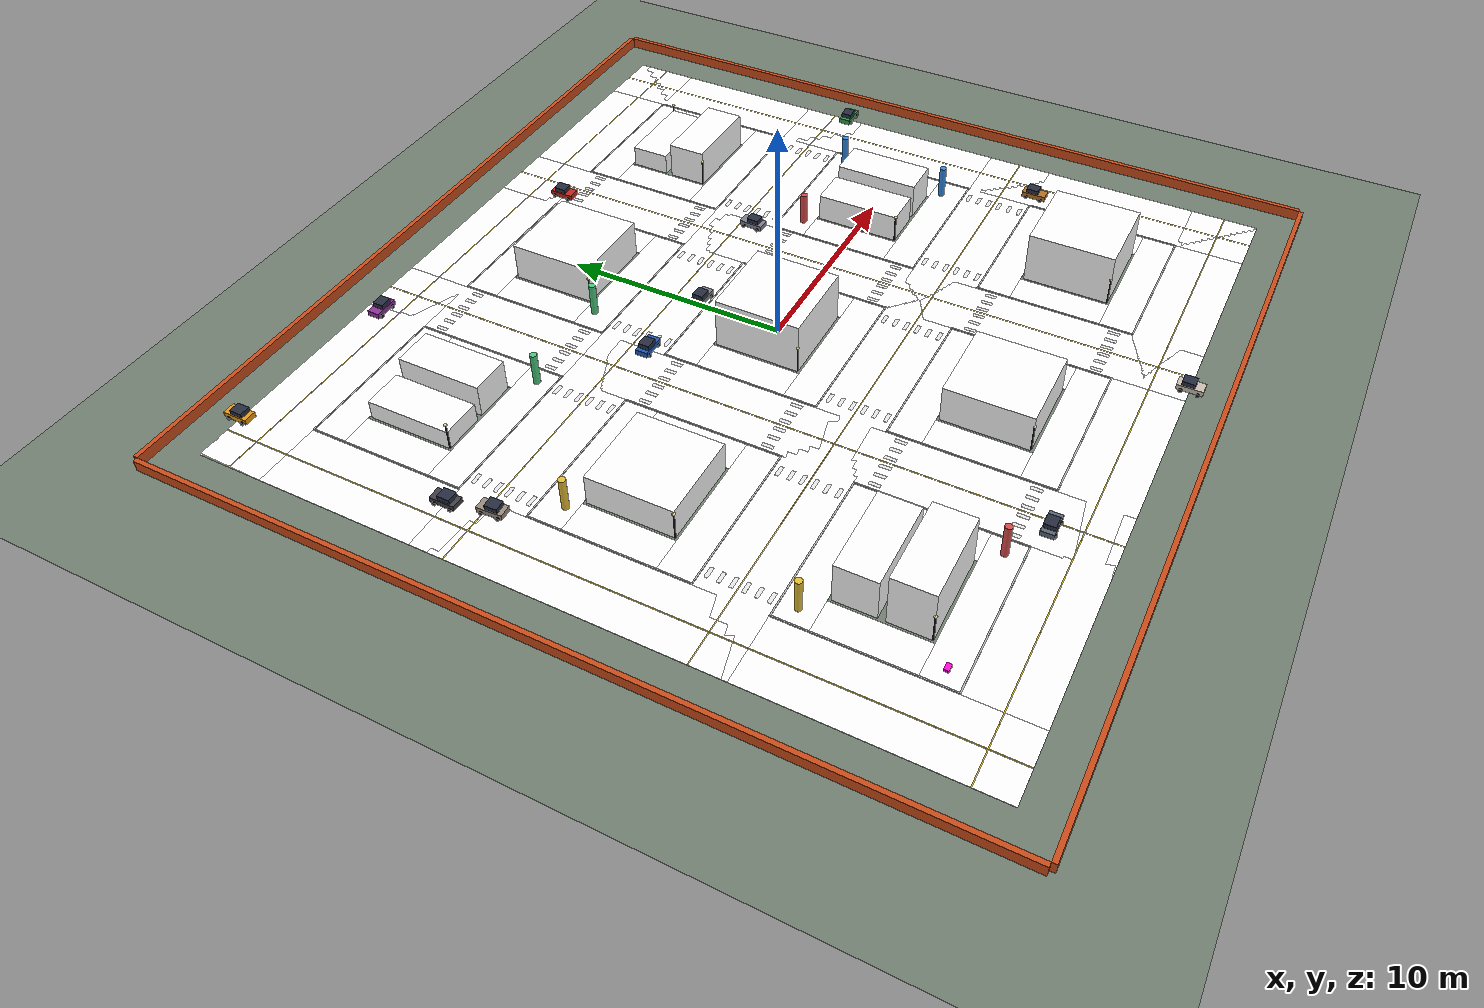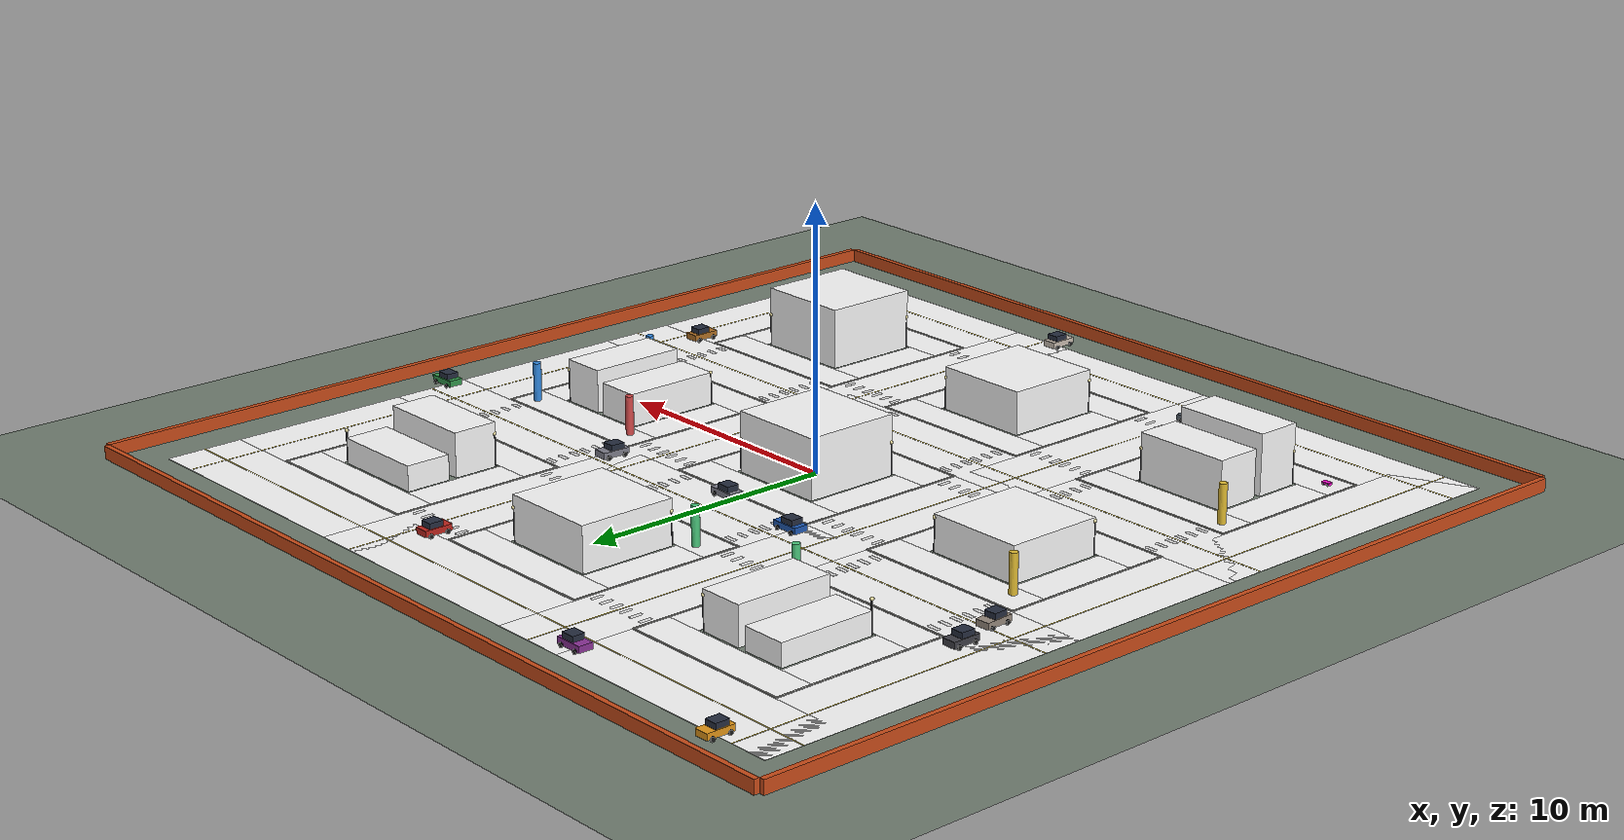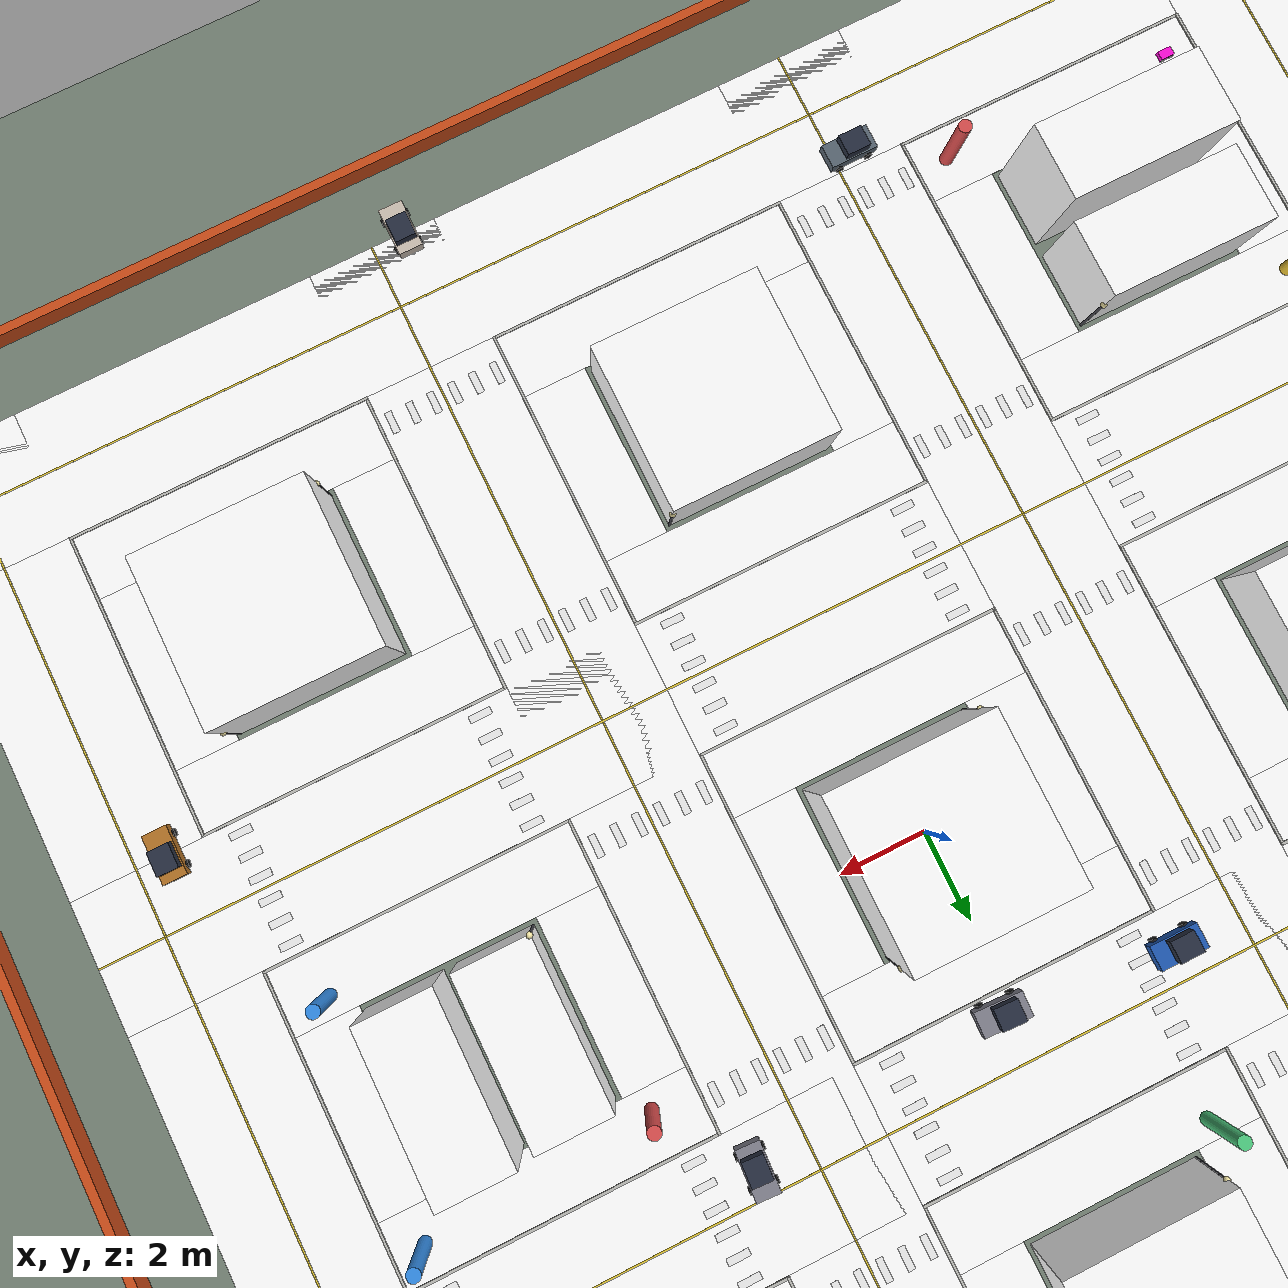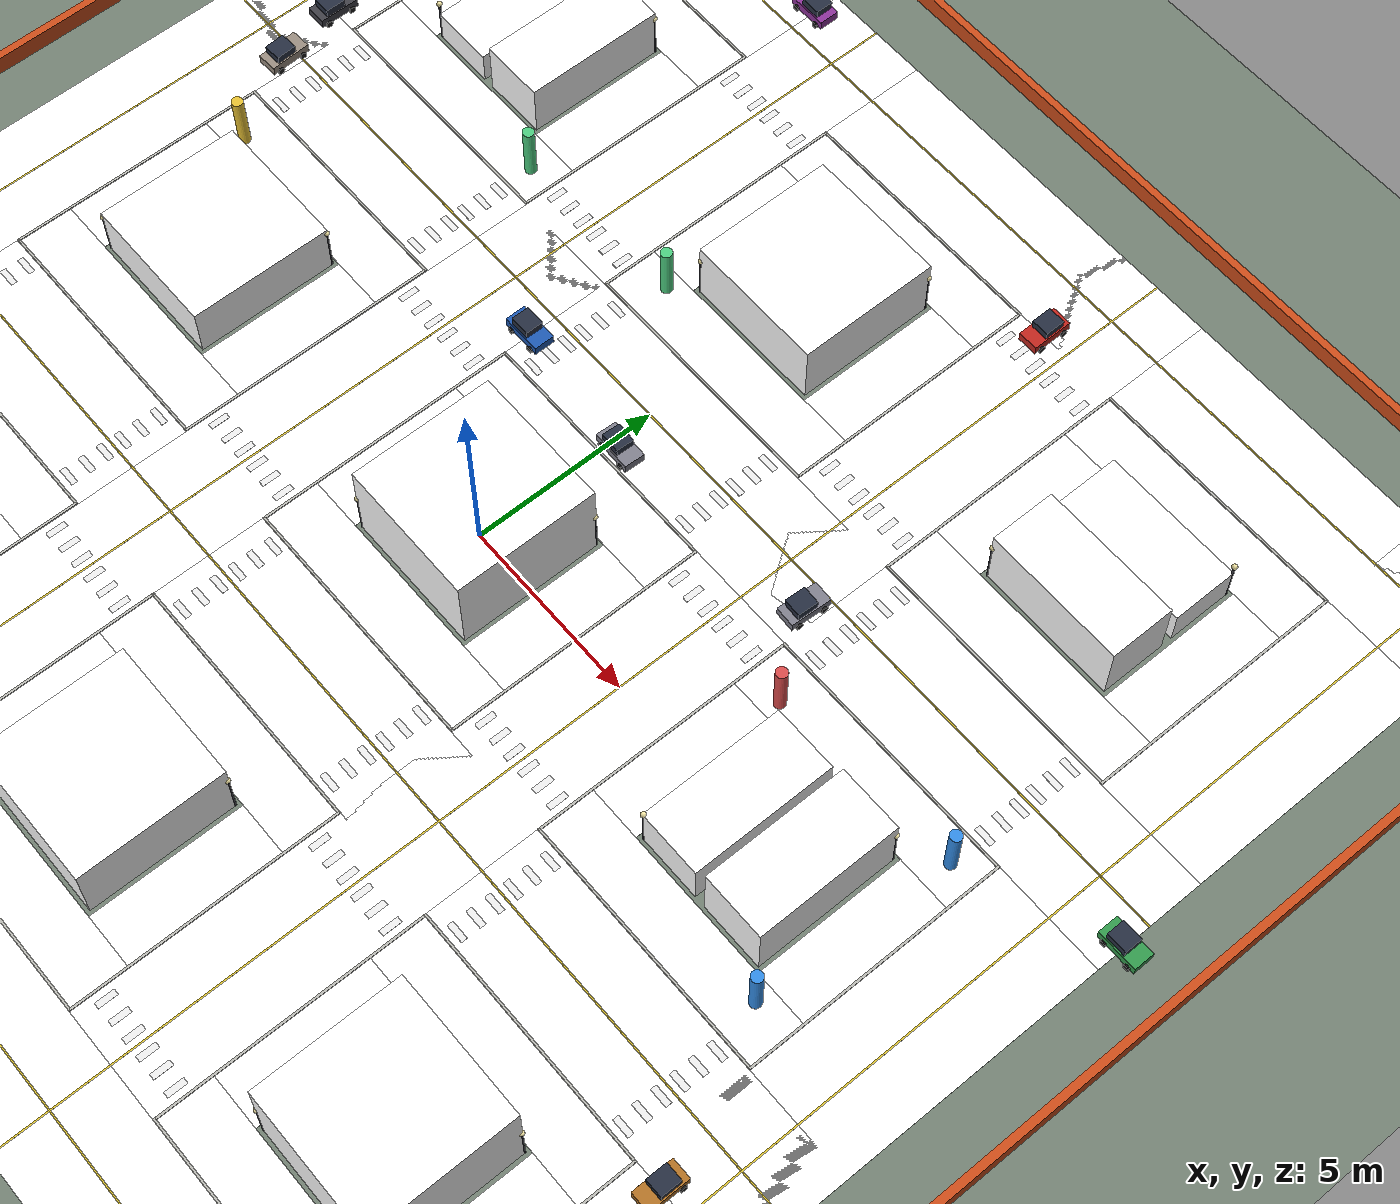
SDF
<?xml version="1.0" ?>
<sdf version="1.9">
  <world name="limo_city_blocks">

    <gui fullscreen="0">
      <plugin filename="MinimalScene" name="3D View">
        <gz-gui>
          <title>3D View</title>
          <property type="bool" key="showTitleBar">false</property>
          <property type="string" key="state">docked</property>
        </gz-gui>
        <engine>ogre2</engine>
        <scene>scene</scene>
        <ambient_light>0.4 0.4 0.4</ambient_light>
        <background_color>0.8 0.8 0.8</background_color>
        <camera_pose>-24.5 -24.5 29.7 0 0.9 0.78</camera_pose>
      </plugin>
      <plugin filename="GzSceneManager" name="Scene Manager"/>
      <plugin filename="InteractiveViewControl" name="Interactive view"/>
      <plugin filename="CameraTracking" name="Camera Tracking"/>
      <plugin filename="MarkerManager" name="Marker Manager"/>
      <plugin filename="WorldControl" name="World control">
        <gz-gui>
          <title>World control</title>
          <property type="bool" key="showTitleBar">false</property>
          <property type="bool" key="resizable">false</property>
          <property type="double" key="height">72</property>
          <property type="double" key="width">121</property>
          <property type="double" key="z">1</property>
          <property type="string" key="state">floating</property>
          <anchors target="3D View">
            <line own="left" target="left"/>
            <line own="bottom" target="bottom"/>
          </anchors>
        </gz-gui>
        <play_pause>true</play_pause>
        <step>true</step>
      </plugin>
      <plugin filename="WorldStats" name="World stats">
        <gz-gui>
          <title>World stats</title>
          <property type="bool" key="showTitleBar">false</property>
          <property type="bool" key="resizable">false</property>
          <property type="double" key="height">110</property>
          <property type="double" key="width">290</property>
          <property type="double" key="z">1</property>
          <property type="string" key="state">floating</property>
          <anchors target="3D View">
            <line own="right" target="right"/>
            <line own="bottom" target="bottom"/>
          </anchors>
        </gz-gui>
        <sim_time>true</sim_time>
        <real_time>true</real_time>
        <real_time_factor>true</real_time_factor>
        <iterations>true</iterations>
      </plugin>
      <plugin filename="EntityTree" name="Entity tree">
        <gz-gui>
          <property type="string" key="state">docked_collapsed</property>
        </gz-gui>
      </plugin>
    </gui>
    <physics name="1ms" type="ode">
      <max_step_size>0.001</max_step_size>
      <real_time_factor>1.0</real_time_factor>
    </physics>

    <plugin filename="gz-sim-physics-system" name="gz::sim::systems::Physics"/>
    <plugin filename="gz-sim-user-commands-system" name="gz::sim::systems::UserCommands"/>
    <plugin filename="gz-sim-scene-broadcaster-system" name="gz::sim::systems::SceneBroadcaster"/>
    <plugin filename="gz-sim-sensors-system" name="gz::sim::systems::Sensors">
      <render_engine>ogre2</render_engine>
    </plugin>
    <plugin filename="gz-sim-imu-system" name="gz::sim::systems::Imu"/>
    <plugin filename="gz-sim-contact-system" name="gz::sim::systems::Contact"/>

    <scene>
      <ambient>0.55 0.55 0.58 1</ambient>
      <background>0.55 0.7 0.9 1</background>
      <sky>
        <time>15</time>
        <sunrise>6</sunrise>
        <sunset>19</sunset>
        <clouds><speed>1.5</speed></clouds>
      </sky>
      <shadows>true</shadows>
    </scene>

    <light type="directional" name="sun">
      <cast_shadows>true</cast_shadows>
      <pose>0 0 10 0 0 0</pose>
      <diffuse>1.0 0.96 0.88 1</diffuse>
      <specular>0.4 0.4 0.35 1</specular>
      <direction>-0.45 0.25 -0.85</direction>
    </light>
    <model name="ground_plane">
      <static>true</static>
      <link name="link">
        <collision name="collision">
          <geometry><plane><normal>0 0 1</normal><size>53 53</size></plane></geometry>
          <surface><friction><ode><mu>0.8</mu><mu2>0.8</mu2></ode></friction></surface>
        </collision>
        <visual name="visual">
          <geometry><plane><normal>0 0 1</normal><size>53 53</size></plane></geometry>
          <material><ambient>0.45 0.5 0.45 1</ambient><diffuse>0.45 0.5 0.45 1</diffuse></material>
        </visual>
      </link>
    </model>

    <!-- ============ ROADS ============ -->
    <model name="road_ns_0">
      <static>true</static>
      <pose>-15.000 0.000 0.005 0 0 0.000</pose>
      <link name="link">

        <visual name="visual"><geometry><box><size>3.000 33.000 0.010</size></box></geometry>
          <material><ambient>1 1 1 1</ambient><diffuse>1 1 1 1</diffuse><pbr><metal><albedo_map>model://city_textures/asphalt.png</albedo_map><roughness>0.85</roughness><metalness>0.0</metalness></metal></pbr></material>
        </visual>
      </link>
    </model>
    <model name="road_ew_0">
      <static>true</static>
      <pose>0.000 -15.000 0.005 0 0 0.000</pose>
      <link name="link">

        <visual name="visual"><geometry><box><size>33.000 3.000 0.010</size></box></geometry>
          <material><ambient>1 1 1 1</ambient><diffuse>1 1 1 1</diffuse><pbr><metal><albedo_map>model://city_textures/asphalt.png</albedo_map><roughness>0.85</roughness><metalness>0.0</metalness></metal></pbr></material>
        </visual>
      </link>
    </model>
    <model name="road_ns_1">
      <static>true</static>
      <pose>-5.000 0.000 0.005 0 0 0.000</pose>
      <link name="link">

        <visual name="visual"><geometry><box><size>3.000 33.000 0.010</size></box></geometry>
          <material><ambient>1 1 1 1</ambient><diffuse>1 1 1 1</diffuse><pbr><metal><albedo_map>model://city_textures/asphalt.png</albedo_map><roughness>0.85</roughness><metalness>0.0</metalness></metal></pbr></material>
        </visual>
      </link>
    </model>
    <model name="road_ew_1">
      <static>true</static>
      <pose>0.000 -5.000 0.005 0 0 0.000</pose>
      <link name="link">

        <visual name="visual"><geometry><box><size>33.000 3.000 0.010</size></box></geometry>
          <material><ambient>1 1 1 1</ambient><diffuse>1 1 1 1</diffuse><pbr><metal><albedo_map>model://city_textures/asphalt.png</albedo_map><roughness>0.85</roughness><metalness>0.0</metalness></metal></pbr></material>
        </visual>
      </link>
    </model>
    <model name="road_ns_2">
      <static>true</static>
      <pose>5.000 0.000 0.005 0 0 0.000</pose>
      <link name="link">

        <visual name="visual"><geometry><box><size>3.000 33.000 0.010</size></box></geometry>
          <material><ambient>1 1 1 1</ambient><diffuse>1 1 1 1</diffuse><pbr><metal><albedo_map>model://city_textures/asphalt.png</albedo_map><roughness>0.85</roughness><metalness>0.0</metalness></metal></pbr></material>
        </visual>
      </link>
    </model>
    <model name="road_ew_2">
      <static>true</static>
      <pose>0.000 5.000 0.005 0 0 0.000</pose>
      <link name="link">

        <visual name="visual"><geometry><box><size>33.000 3.000 0.010</size></box></geometry>
          <material><ambient>1 1 1 1</ambient><diffuse>1 1 1 1</diffuse><pbr><metal><albedo_map>model://city_textures/asphalt.png</albedo_map><roughness>0.85</roughness><metalness>0.0</metalness></metal></pbr></material>
        </visual>
      </link>
    </model>
    <model name="road_ns_3">
      <static>true</static>
      <pose>15.000 0.000 0.005 0 0 0.000</pose>
      <link name="link">

        <visual name="visual"><geometry><box><size>3.000 33.000 0.010</size></box></geometry>
          <material><ambient>1 1 1 1</ambient><diffuse>1 1 1 1</diffuse><pbr><metal><albedo_map>model://city_textures/asphalt.png</albedo_map><roughness>0.85</roughness><metalness>0.0</metalness></metal></pbr></material>
        </visual>
      </link>
    </model>
    <model name="road_ew_3">
      <static>true</static>
      <pose>0.000 15.000 0.005 0 0 0.000</pose>
      <link name="link">

        <visual name="visual"><geometry><box><size>33.000 3.000 0.010</size></box></geometry>
          <material><ambient>1 1 1 1</ambient><diffuse>1 1 1 1</diffuse><pbr><metal><albedo_map>model://city_textures/asphalt.png</albedo_map><roughness>0.85</roughness><metalness>0.0</metalness></metal></pbr></material>
        </visual>
      </link>
    </model>
    <model name="line_ns_0">
      <static>true</static>
      <pose>-15.000 0.000 0.011 0 0 0.000</pose>
      <link name="link">

        <visual name="visual"><geometry><box><size>0.040 33.000 0.002</size></box></geometry>
          <material><ambient>0.85 0.75 0.2 1</ambient><diffuse>0.85 0.75 0.2 1</diffuse></material>
        </visual>
      </link>
    </model>
    <model name="line_ew_0">
      <static>true</static>
      <pose>0.000 -15.000 0.011 0 0 0.000</pose>
      <link name="link">

        <visual name="visual"><geometry><box><size>33.000 0.040 0.002</size></box></geometry>
          <material><ambient>0.85 0.75 0.2 1</ambient><diffuse>0.85 0.75 0.2 1</diffuse></material>
        </visual>
      </link>
    </model>
    <model name="line_ns_1">
      <static>true</static>
      <pose>-5.000 0.000 0.011 0 0 0.000</pose>
      <link name="link">

        <visual name="visual"><geometry><box><size>0.040 33.000 0.002</size></box></geometry>
          <material><ambient>0.85 0.75 0.2 1</ambient><diffuse>0.85 0.75 0.2 1</diffuse></material>
        </visual>
      </link>
    </model>
    <model name="line_ew_1">
      <static>true</static>
      <pose>0.000 -5.000 0.011 0 0 0.000</pose>
      <link name="link">

        <visual name="visual"><geometry><box><size>33.000 0.040 0.002</size></box></geometry>
          <material><ambient>0.85 0.75 0.2 1</ambient><diffuse>0.85 0.75 0.2 1</diffuse></material>
        </visual>
      </link>
    </model>
    <model name="line_ns_2">
      <static>true</static>
      <pose>5.000 0.000 0.011 0 0 0.000</pose>
      <link name="link">

        <visual name="visual"><geometry><box><size>0.040 33.000 0.002</size></box></geometry>
          <material><ambient>0.85 0.75 0.2 1</ambient><diffuse>0.85 0.75 0.2 1</diffuse></material>
        </visual>
      </link>
    </model>
    <model name="line_ew_2">
      <static>true</static>
      <pose>0.000 5.000 0.011 0 0 0.000</pose>
      <link name="link">

        <visual name="visual"><geometry><box><size>33.000 0.040 0.002</size></box></geometry>
          <material><ambient>0.85 0.75 0.2 1</ambient><diffuse>0.85 0.75 0.2 1</diffuse></material>
        </visual>
      </link>
    </model>
    <model name="line_ns_3">
      <static>true</static>
      <pose>15.000 0.000 0.011 0 0 0.000</pose>
      <link name="link">

        <visual name="visual"><geometry><box><size>0.040 33.000 0.002</size></box></geometry>
          <material><ambient>0.85 0.75 0.2 1</ambient><diffuse>0.85 0.75 0.2 1</diffuse></material>
        </visual>
      </link>
    </model>
    <model name="line_ew_3">
      <static>true</static>
      <pose>0.000 15.000 0.011 0 0 0.000</pose>
      <link name="link">

        <visual name="visual"><geometry><box><size>33.000 0.040 0.002</size></box></geometry>
          <material><ambient>0.85 0.75 0.2 1</ambient><diffuse>0.85 0.75 0.2 1</diffuse></material>
        </visual>
      </link>
    </model>

    <!-- ============ SIDEWALKS ============ -->
    <model name="walk_s_0_0">
      <static>true</static>
      <pose>-10.000 -12.750 0.008 0 0 0.000</pose>
      <link name="link">

        <visual name="visual"><geometry><box><size>7.000 1.500 0.012</size></box></geometry>
          <material><ambient>1 1 1 1</ambient><diffuse>1 1 1 1</diffuse><pbr><metal><albedo_map>model://city_textures/paving.png</albedo_map><roughness>0.85</roughness><metalness>0.0</metalness></metal></pbr></material>
        </visual>
      </link>
    </model>
    <model name="walk_n_0_0">
      <static>true</static>
      <pose>-10.000 -7.250 0.008 0 0 0.000</pose>
      <link name="link">

        <visual name="visual"><geometry><box><size>7.000 1.500 0.012</size></box></geometry>
          <material><ambient>1 1 1 1</ambient><diffuse>1 1 1 1</diffuse><pbr><metal><albedo_map>model://city_textures/paving.png</albedo_map><roughness>0.85</roughness><metalness>0.0</metalness></metal></pbr></material>
        </visual>
      </link>
    </model>
    <model name="walk_w_0_0">
      <static>true</static>
      <pose>-12.750 -10.000 0.008 0 0 0.000</pose>
      <link name="link">

        <visual name="visual"><geometry><box><size>1.500 4.000 0.012</size></box></geometry>
          <material><ambient>1 1 1 1</ambient><diffuse>1 1 1 1</diffuse><pbr><metal><albedo_map>model://city_textures/paving.png</albedo_map><roughness>0.85</roughness><metalness>0.0</metalness></metal></pbr></material>
        </visual>
      </link>
    </model>
    <model name="walk_e_0_0">
      <static>true</static>
      <pose>-7.250 -10.000 0.008 0 0 0.000</pose>
      <link name="link">

        <visual name="visual"><geometry><box><size>1.500 4.000 0.012</size></box></geometry>
          <material><ambient>1 1 1 1</ambient><diffuse>1 1 1 1</diffuse><pbr><metal><albedo_map>model://city_textures/paving.png</albedo_map><roughness>0.85</roughness><metalness>0.0</metalness></metal></pbr></material>
        </visual>
      </link>
    </model>
    <model name="walk_s_0_1">
      <static>true</static>
      <pose>-10.000 -2.750 0.008 0 0 0.000</pose>
      <link name="link">

        <visual name="visual"><geometry><box><size>7.000 1.500 0.012</size></box></geometry>
          <material><ambient>1 1 1 1</ambient><diffuse>1 1 1 1</diffuse><pbr><metal><albedo_map>model://city_textures/paving.png</albedo_map><roughness>0.85</roughness><metalness>0.0</metalness></metal></pbr></material>
        </visual>
      </link>
    </model>
    <model name="walk_n_0_1">
      <static>true</static>
      <pose>-10.000 2.750 0.008 0 0 0.000</pose>
      <link name="link">

        <visual name="visual"><geometry><box><size>7.000 1.500 0.012</size></box></geometry>
          <material><ambient>1 1 1 1</ambient><diffuse>1 1 1 1</diffuse><pbr><metal><albedo_map>model://city_textures/paving.png</albedo_map><roughness>0.85</roughness><metalness>0.0</metalness></metal></pbr></material>
        </visual>
      </link>
    </model>
    <model name="walk_w_0_1">
      <static>true</static>
      <pose>-12.750 0.000 0.008 0 0 0.000</pose>
      <link name="link">

        <visual name="visual"><geometry><box><size>1.500 4.000 0.012</size></box></geometry>
          <material><ambient>1 1 1 1</ambient><diffuse>1 1 1 1</diffuse><pbr><metal><albedo_map>model://city_textures/paving.png</albedo_map><roughness>0.85</roughness><metalness>0.0</metalness></metal></pbr></material>
        </visual>
      </link>
    </model>
    <model name="walk_e_0_1">
      <static>true</static>
      <pose>-7.250 0.000 0.008 0 0 0.000</pose>
      <link name="link">

        <visual name="visual"><geometry><box><size>1.500 4.000 0.012</size></box></geometry>
          <material><ambient>1 1 1 1</ambient><diffuse>1 1 1 1</diffuse><pbr><metal><albedo_map>model://city_textures/paving.png</albedo_map><roughness>0.85</roughness><metalness>0.0</metalness></metal></pbr></material>
        </visual>
      </link>
    </model>
    <model name="walk_s_0_2">
      <static>true</static>
      <pose>-10.000 7.250 0.008 0 0 0.000</pose>
      <link name="link">

        <visual name="visual"><geometry><box><size>7.000 1.500 0.012</size></box></geometry>
          <material><ambient>1 1 1 1</ambient><diffuse>1 1 1 1</diffuse><pbr><metal><albedo_map>model://city_textures/paving.png</albedo_map><roughness>0.85</roughness><metalness>0.0</metalness></metal></pbr></material>
        </visual>
      </link>
    </model>
    <model name="walk_n_0_2">
      <static>true</static>
      <pose>-10.000 12.750 0.008 0 0 0.000</pose>
      <link name="link">

        <visual name="visual"><geometry><box><size>7.000 1.500 0.012</size></box></geometry>
          <material><ambient>1 1 1 1</ambient><diffuse>1 1 1 1</diffuse><pbr><metal><albedo_map>model://city_textures/paving.png</albedo_map><roughness>0.85</roughness><metalness>0.0</metalness></metal></pbr></material>
        </visual>
      </link>
    </model>
    <model name="walk_w_0_2">
      <static>true</static>
      <pose>-12.750 10.000 0.008 0 0 0.000</pose>
      <link name="link">

        <visual name="visual"><geometry><box><size>1.500 4.000 0.012</size></box></geometry>
          <material><ambient>1 1 1 1</ambient><diffuse>1 1 1 1</diffuse><pbr><metal><albedo_map>model://city_textures/paving.png</albedo_map><roughness>0.85</roughness><metalness>0.0</metalness></metal></pbr></material>
        </visual>
      </link>
    </model>
    <model name="walk_e_0_2">
      <static>true</static>
      <pose>-7.250 10.000 0.008 0 0 0.000</pose>
      <link name="link">

        <visual name="visual"><geometry><box><size>1.500 4.000 0.012</size></box></geometry>
          <material><ambient>1 1 1 1</ambient><diffuse>1 1 1 1</diffuse><pbr><metal><albedo_map>model://city_textures/paving.png</albedo_map><roughness>0.85</roughness><metalness>0.0</metalness></metal></pbr></material>
        </visual>
      </link>
    </model>
    <model name="walk_s_1_0">
      <static>true</static>
      <pose>0.000 -12.750 0.008 0 0 0.000</pose>
      <link name="link">

        <visual name="visual"><geometry><box><size>7.000 1.500 0.012</size></box></geometry>
          <material><ambient>1 1 1 1</ambient><diffuse>1 1 1 1</diffuse><pbr><metal><albedo_map>model://city_textures/paving.png</albedo_map><roughness>0.85</roughness><metalness>0.0</metalness></metal></pbr></material>
        </visual>
      </link>
    </model>
    <model name="walk_n_1_0">
      <static>true</static>
      <pose>0.000 -7.250 0.008 0 0 0.000</pose>
      <link name="link">

        <visual name="visual"><geometry><box><size>7.000 1.500 0.012</size></box></geometry>
          <material><ambient>1 1 1 1</ambient><diffuse>1 1 1 1</diffuse><pbr><metal><albedo_map>model://city_textures/paving.png</albedo_map><roughness>0.85</roughness><metalness>0.0</metalness></metal></pbr></material>
        </visual>
      </link>
    </model>
    <model name="walk_w_1_0">
      <static>true</static>
      <pose>-2.750 -10.000 0.008 0 0 0.000</pose>
      <link name="link">

        <visual name="visual"><geometry><box><size>1.500 4.000 0.012</size></box></geometry>
          <material><ambient>1 1 1 1</ambient><diffuse>1 1 1 1</diffuse><pbr><metal><albedo_map>model://city_textures/paving.png</albedo_map><roughness>0.85</roughness><metalness>0.0</metalness></metal></pbr></material>
        </visual>
      </link>
    </model>
    <model name="walk_e_1_0">
      <static>true</static>
      <pose>2.750 -10.000 0.008 0 0 0.000</pose>
      <link name="link">

        <visual name="visual"><geometry><box><size>1.500 4.000 0.012</size></box></geometry>
          <material><ambient>1 1 1 1</ambient><diffuse>1 1 1 1</diffuse><pbr><metal><albedo_map>model://city_textures/paving.png</albedo_map><roughness>0.85</roughness><metalness>0.0</metalness></metal></pbr></material>
        </visual>
      </link>
    </model>
    <model name="walk_s_1_1">
      <static>true</static>
      <pose>0.000 -2.750 0.008 0 0 0.000</pose>
      <link name="link">

        <visual name="visual"><geometry><box><size>7.000 1.500 0.012</size></box></geometry>
          <material><ambient>1 1 1 1</ambient><diffuse>1 1 1 1</diffuse><pbr><metal><albedo_map>model://city_textures/paving.png</albedo_map><roughness>0.85</roughness><metalness>0.0</metalness></metal></pbr></material>
        </visual>
      </link>
    </model>
    <model name="walk_n_1_1">
      <static>true</static>
      <pose>0.000 2.750 0.008 0 0 0.000</pose>
      <link name="link">

        <visual name="visual"><geometry><box><size>7.000 1.500 0.012</size></box></geometry>
          <material><ambient>1 1 1 1</ambient><diffuse>1 1 1 1</diffuse><pbr><metal><albedo_map>model://city_textures/paving.png</albedo_map><roughness>0.85</roughness><metalness>0.0</metalness></metal></pbr></material>
        </visual>
      </link>
    </model>
    <model name="walk_w_1_1">
      <static>true</static>
      <pose>-2.750 0.000 0.008 0 0 0.000</pose>
      <link name="link">

        <visual name="visual"><geometry><box><size>1.500 4.000 0.012</size></box></geometry>
          <material><ambient>1 1 1 1</ambient><diffuse>1 1 1 1</diffuse><pbr><metal><albedo_map>model://city_textures/paving.png</albedo_map><roughness>0.85</roughness><metalness>0.0</metalness></metal></pbr></material>
        </visual>
      </link>
    </model>
    <model name="walk_e_1_1">
      <static>true</static>
      <pose>2.750 0.000 0.008 0 0 0.000</pose>
      <link name="link">

        <visual name="visual"><geometry><box><size>1.500 4.000 0.012</size></box></geometry>
          <material><ambient>1 1 1 1</ambient><diffuse>1 1 1 1</diffuse><pbr><metal><albedo_map>model://city_textures/paving.png</albedo_map><roughness>0.85</roughness><metalness>0.0</metalness></metal></pbr></material>
        </visual>
      </link>
    </model>
    <model name="walk_s_1_2">
      <static>true</static>
      <pose>0.000 7.250 0.008 0 0 0.000</pose>
      <link name="link">

        <visual name="visual"><geometry><box><size>7.000 1.500 0.012</size></box></geometry>
          <material><ambient>1 1 1 1</ambient><diffuse>1 1 1 1</diffuse><pbr><metal><albedo_map>model://city_textures/paving.png</albedo_map><roughness>0.85</roughness><metalness>0.0</metalness></metal></pbr></material>
        </visual>
      </link>
    </model>
    <model name="walk_n_1_2">
      <static>true</static>
      <pose>0.000 12.750 0.008 0 0 0.000</pose>
      <link name="link">

        <visual name="visual"><geometry><box><size>7.000 1.500 0.012</size></box></geometry>
          <material><ambient>1 1 1 1</ambient><diffuse>1 1 1 1</diffuse><pbr><metal><albedo_map>model://city_textures/paving.png</albedo_map><roughness>0.85</roughness><metalness>0.0</metalness></metal></pbr></material>
        </visual>
      </link>
    </model>
    <model name="walk_w_1_2">
      <static>true</static>
      <pose>-2.750 10.000 0.008 0 0 0.000</pose>
      <link name="link">

        <visual name="visual"><geometry><box><size>1.500 4.000 0.012</size></box></geometry>
          <material><ambient>1 1 1 1</ambient><diffuse>1 1 1 1</diffuse><pbr><metal><albedo_map>model://city_textures/paving.png</albedo_map><roughness>0.85</roughness><metalness>0.0</metalness></metal></pbr></material>
        </visual>
      </link>
    </model>
    <model name="walk_e_1_2">
      <static>true</static>
      <pose>2.750 10.000 0.008 0 0 0.000</pose>
      <link name="link">

        <visual name="visual"><geometry><box><size>1.500 4.000 0.012</size></box></geometry>
          <material><ambient>1 1 1 1</ambient><diffuse>1 1 1 1</diffuse><pbr><metal><albedo_map>model://city_textures/paving.png</albedo_map><roughness>0.85</roughness><metalness>0.0</metalness></metal></pbr></material>
        </visual>
      </link>
    </model>
    <model name="walk_s_2_0">
      <static>true</static>
      <pose>10.000 -12.750 0.008 0 0 0.000</pose>
      <link name="link">

        <visual name="visual"><geometry><box><size>7.000 1.500 0.012</size></box></geometry>
          <material><ambient>1 1 1 1</ambient><diffuse>1 1 1 1</diffuse><pbr><metal><albedo_map>model://city_textures/paving.png</albedo_map><roughness>0.85</roughness><metalness>0.0</metalness></metal></pbr></material>
        </visual>
      </link>
    </model>
    <model name="walk_n_2_0">
      <static>true</static>
      <pose>10.000 -7.250 0.008 0 0 0.000</pose>
      <link name="link">

        <visual name="visual"><geometry><box><size>7.000 1.500 0.012</size></box></geometry>
          <material><ambient>1 1 1 1</ambient><diffuse>1 1 1 1</diffuse><pbr><metal><albedo_map>model://city_textures/paving.png</albedo_map><roughness>0.85</roughness><metalness>0.0</metalness></metal></pbr></material>
        </visual>
      </link>
    </model>
    <model name="walk_w_2_0">
      <static>true</static>
      <pose>7.250 -10.000 0.008 0 0 0.000</pose>
      <link name="link">

        <visual name="visual"><geometry><box><size>1.500 4.000 0.012</size></box></geometry>
          <material><ambient>1 1 1 1</ambient><diffuse>1 1 1 1</diffuse><pbr><metal><albedo_map>model://city_textures/paving.png</albedo_map><roughness>0.85</roughness><metalness>0.0</metalness></metal></pbr></material>
        </visual>
      </link>
    </model>
    <model name="walk_e_2_0">
      <static>true</static>
      <pose>12.750 -10.000 0.008 0 0 0.000</pose>
      <link name="link">

        <visual name="visual"><geometry><box><size>1.500 4.000 0.012</size></box></geometry>
          <material><ambient>1 1 1 1</ambient><diffuse>1 1 1 1</diffuse><pbr><metal><albedo_map>model://city_textures/paving.png</albedo_map><roughness>0.85</roughness><metalness>0.0</metalness></metal></pbr></material>
        </visual>
      </link>
    </model>
    <model name="walk_s_2_1">
      <static>true</static>
      <pose>10.000 -2.750 0.008 0 0 0.000</pose>
      <link name="link">

        <visual name="visual"><geometry><box><size>7.000 1.500 0.012</size></box></geometry>
          <material><ambient>1 1 1 1</ambient><diffuse>1 1 1 1</diffuse><pbr><metal><albedo_map>model://city_textures/paving.png</albedo_map><roughness>0.85</roughness><metalness>0.0</metalness></metal></pbr></material>
        </visual>
      </link>
    </model>
    <model name="walk_n_2_1">
      <static>true</static>
      <pose>10.000 2.750 0.008 0 0 0.000</pose>
      <link name="link">

        <visual name="visual"><geometry><box><size>7.000 1.500 0.012</size></box></geometry>
          <material><ambient>1 1 1 1</ambient><diffuse>1 1 1 1</diffuse><pbr><metal><albedo_map>model://city_textures/paving.png</albedo_map><roughness>0.85</roughness><metalness>0.0</metalness></metal></pbr></material>
        </visual>
      </link>
    </model>
    <model name="walk_w_2_1">
      <static>true</static>
      <pose>7.250 0.000 0.008 0 0 0.000</pose>
      <link name="link">

        <visual name="visual"><geometry><box><size>1.500 4.000 0.012</size></box></geometry>
          <material><ambient>1 1 1 1</ambient><diffuse>1 1 1 1</diffuse><pbr><metal><albedo_map>model://city_textures/paving.png</albedo_map><roughness>0.85</roughness><metalness>0.0</metalness></metal></pbr></material>
        </visual>
      </link>
    </model>
    <model name="walk_e_2_1">
      <static>true</static>
      <pose>12.750 0.000 0.008 0 0 0.000</pose>
      <link name="link">

        <visual name="visual"><geometry><box><size>1.500 4.000 0.012</size></box></geometry>
          <material><ambient>1 1 1 1</ambient><diffuse>1 1 1 1</diffuse><pbr><metal><albedo_map>model://city_textures/paving.png</albedo_map><roughness>0.85</roughness><metalness>0.0</metalness></metal></pbr></material>
        </visual>
      </link>
    </model>
    <model name="walk_s_2_2">
      <static>true</static>
      <pose>10.000 7.250 0.008 0 0 0.000</pose>
      <link name="link">

        <visual name="visual"><geometry><box><size>7.000 1.500 0.012</size></box></geometry>
          <material><ambient>1 1 1 1</ambient><diffuse>1 1 1 1</diffuse><pbr><metal><albedo_map>model://city_textures/paving.png</albedo_map><roughness>0.85</roughness><metalness>0.0</metalness></metal></pbr></material>
        </visual>
      </link>
    </model>
    <model name="walk_n_2_2">
      <static>true</static>
      <pose>10.000 12.750 0.008 0 0 0.000</pose>
      <link name="link">

        <visual name="visual"><geometry><box><size>7.000 1.500 0.012</size></box></geometry>
          <material><ambient>1 1 1 1</ambient><diffuse>1 1 1 1</diffuse><pbr><metal><albedo_map>model://city_textures/paving.png</albedo_map><roughness>0.85</roughness><metalness>0.0</metalness></metal></pbr></material>
        </visual>
      </link>
    </model>
    <model name="walk_w_2_2">
      <static>true</static>
      <pose>7.250 10.000 0.008 0 0 0.000</pose>
      <link name="link">

        <visual name="visual"><geometry><box><size>1.500 4.000 0.012</size></box></geometry>
          <material><ambient>1 1 1 1</ambient><diffuse>1 1 1 1</diffuse><pbr><metal><albedo_map>model://city_textures/paving.png</albedo_map><roughness>0.85</roughness><metalness>0.0</metalness></metal></pbr></material>
        </visual>
      </link>
    </model>
    <model name="walk_e_2_2">
      <static>true</static>
      <pose>12.750 10.000 0.008 0 0 0.000</pose>
      <link name="link">

        <visual name="visual"><geometry><box><size>1.500 4.000 0.012</size></box></geometry>
          <material><ambient>1 1 1 1</ambient><diffuse>1 1 1 1</diffuse><pbr><metal><albedo_map>model://city_textures/paving.png</albedo_map><roughness>0.85</roughness><metalness>0.0</metalness></metal></pbr></material>
        </visual>
      </link>
    </model>
    <model name="curb_s_0_0">
      <static>true</static>
      <pose>-10.000 -13.470 0.020 0 0 0.000</pose>
      <link name="link">

        <visual name="visual"><geometry><box><size>7.000 0.060 0.040</size></box></geometry>
          <material><ambient>0.72 0.72 0.7 1</ambient><diffuse>0.72 0.72 0.7 1</diffuse></material>
        </visual>
      </link>
    </model>
    <model name="curb_n_0_0">
      <static>true</static>
      <pose>-10.000 -6.530 0.020 0 0 0.000</pose>
      <link name="link">

        <visual name="visual"><geometry><box><size>7.000 0.060 0.040</size></box></geometry>
          <material><ambient>0.72 0.72 0.7 1</ambient><diffuse>0.72 0.72 0.7 1</diffuse></material>
        </visual>
      </link>
    </model>
    <model name="curb_w_0_0">
      <static>true</static>
      <pose>-13.470 -10.000 0.020 0 0 0.000</pose>
      <link name="link">

        <visual name="visual"><geometry><box><size>0.060 7.000 0.040</size></box></geometry>
          <material><ambient>0.72 0.72 0.7 1</ambient><diffuse>0.72 0.72 0.7 1</diffuse></material>
        </visual>
      </link>
    </model>
    <model name="curb_e_0_0">
      <static>true</static>
      <pose>-6.530 -10.000 0.020 0 0 0.000</pose>
      <link name="link">

        <visual name="visual"><geometry><box><size>0.060 7.000 0.040</size></box></geometry>
          <material><ambient>0.72 0.72 0.7 1</ambient><diffuse>0.72 0.72 0.7 1</diffuse></material>
        </visual>
      </link>
    </model>
    <model name="curb_s_0_1">
      <static>true</static>
      <pose>-10.000 -3.470 0.020 0 0 0.000</pose>
      <link name="link">

        <visual name="visual"><geometry><box><size>7.000 0.060 0.040</size></box></geometry>
          <material><ambient>0.72 0.72 0.7 1</ambient><diffuse>0.72 0.72 0.7 1</diffuse></material>
        </visual>
      </link>
    </model>
    <model name="curb_n_0_1">
      <static>true</static>
      <pose>-10.000 3.470 0.020 0 0 0.000</pose>
      <link name="link">

        <visual name="visual"><geometry><box><size>7.000 0.060 0.040</size></box></geometry>
          <material><ambient>0.72 0.72 0.7 1</ambient><diffuse>0.72 0.72 0.7 1</diffuse></material>
        </visual>
      </link>
    </model>
    <model name="curb_w_0_1">
      <static>true</static>
      <pose>-13.470 0.000 0.020 0 0 0.000</pose>
      <link name="link">

        <visual name="visual"><geometry><box><size>0.060 7.000 0.040</size></box></geometry>
          <material><ambient>0.72 0.72 0.7 1</ambient><diffuse>0.72 0.72 0.7 1</diffuse></material>
        </visual>
      </link>
    </model>
    <model name="curb_e_0_1">
      <static>true</static>
      <pose>-6.530 0.000 0.020 0 0 0.000</pose>
      <link name="link">

        <visual name="visual"><geometry><box><size>0.060 7.000 0.040</size></box></geometry>
          <material><ambient>0.72 0.72 0.7 1</ambient><diffuse>0.72 0.72 0.7 1</diffuse></material>
        </visual>
      </link>
    </model>
    <model name="curb_s_0_2">
      <static>true</static>
      <pose>-10.000 6.530 0.020 0 0 0.000</pose>
      <link name="link">

        <visual name="visual"><geometry><box><size>7.000 0.060 0.040</size></box></geometry>
          <material><ambient>0.72 0.72 0.7 1</ambient><diffuse>0.72 0.72 0.7 1</diffuse></material>
        </visual>
      </link>
    </model>
    <model name="curb_n_0_2">
      <static>true</static>
      <pose>-10.000 13.470 0.020 0 0 0.000</pose>
      <link name="link">

        <visual name="visual"><geometry><box><size>7.000 0.060 0.040</size></box></geometry>
          <material><ambient>0.72 0.72 0.7 1</ambient><diffuse>0.72 0.72 0.7 1</diffuse></material>
        </visual>
      </link>
    </model>
    <model name="curb_w_0_2">
      <static>true</static>
      <pose>-13.470 10.000 0.020 0 0 0.000</pose>
      <link name="link">

        <visual name="visual"><geometry><box><size>0.060 7.000 0.040</size></box></geometry>
          <material><ambient>0.72 0.72 0.7 1</ambient><diffuse>0.72 0.72 0.7 1</diffuse></material>
        </visual>
      </link>
    </model>
    <model name="curb_e_0_2">
      <static>true</static>
      <pose>-6.530 10.000 0.020 0 0 0.000</pose>
      <link name="link">

        <visual name="visual"><geometry><box><size>0.060 7.000 0.040</size></box></geometry>
          <material><ambient>0.72 0.72 0.7 1</ambient><diffuse>0.72 0.72 0.7 1</diffuse></material>
        </visual>
      </link>
    </model>
    <model name="curb_s_1_0">
      <static>true</static>
      <pose>0.000 -13.470 0.020 0 0 0.000</pose>
      <link name="link">

        <visual name="visual"><geometry><box><size>7.000 0.060 0.040</size></box></geometry>
          <material><ambient>0.72 0.72 0.7 1</ambient><diffuse>0.72 0.72 0.7 1</diffuse></material>
        </visual>
      </link>
    </model>
    <model name="curb_n_1_0">
      <static>true</static>
      <pose>0.000 -6.530 0.020 0 0 0.000</pose>
      <link name="link">

        <visual name="visual"><geometry><box><size>7.000 0.060 0.040</size></box></geometry>
          <material><ambient>0.72 0.72 0.7 1</ambient><diffuse>0.72 0.72 0.7 1</diffuse></material>
        </visual>
      </link>
    </model>
    <model name="curb_w_1_0">
      <static>true</static>
      <pose>-3.470 -10.000 0.020 0 0 0.000</pose>
      <link name="link">

        <visual name="visual"><geometry><box><size>0.060 7.000 0.040</size></box></geometry>
          <material><ambient>0.72 0.72 0.7 1</ambient><diffuse>0.72 0.72 0.7 1</diffuse></material>
        </visual>
      </link>
    </model>
    <model name="curb_e_1_0">
      <static>true</static>
      <pose>3.470 -10.000 0.020 0 0 0.000</pose>
      <link name="link">

        <visual name="visual"><geometry><box><size>0.060 7.000 0.040</size></box></geometry>
          <material><ambient>0.72 0.72 0.7 1</ambient><diffuse>0.72 0.72 0.7 1</diffuse></material>
        </visual>
      </link>
    </model>
    <model name="curb_s_1_1">
      <static>true</static>
      <pose>0.000 -3.470 0.020 0 0 0.000</pose>
      <link name="link">

        <visual name="visual"><geometry><box><size>7.000 0.060 0.040</size></box></geometry>
          <material><ambient>0.72 0.72 0.7 1</ambient><diffuse>0.72 0.72 0.7 1</diffuse></material>
        </visual>
      </link>
    </model>
    <model name="curb_n_1_1">
      <static>true</static>
      <pose>0.000 3.470 0.020 0 0 0.000</pose>
      <link name="link">

        <visual name="visual"><geometry><box><size>7.000 0.060 0.040</size></box></geometry>
          <material><ambient>0.72 0.72 0.7 1</ambient><diffuse>0.72 0.72 0.7 1</diffuse></material>
        </visual>
      </link>
    </model>
    <model name="curb_w_1_1">
      <static>true</static>
      <pose>-3.470 0.000 0.020 0 0 0.000</pose>
      <link name="link">

        <visual name="visual"><geometry><box><size>0.060 7.000 0.040</size></box></geometry>
          <material><ambient>0.72 0.72 0.7 1</ambient><diffuse>0.72 0.72 0.7 1</diffuse></material>
        </visual>
      </link>
    </model>
    <model name="curb_e_1_1">
      <static>true</static>
      <pose>3.470 0.000 0.020 0 0 0.000</pose>
      <link name="link">

        <visual name="visual"><geometry><box><size>0.060 7.000 0.040</size></box></geometry>
          <material><ambient>0.72 0.72 0.7 1</ambient><diffuse>0.72 0.72 0.7 1</diffuse></material>
        </visual>
      </link>
    </model>
    <model name="curb_s_1_2">
      <static>true</static>
      <pose>0.000 6.530 0.020 0 0 0.000</pose>
      <link name="link">

        <visual name="visual"><geometry><box><size>7.000 0.060 0.040</size></box></geometry>
          <material><ambient>0.72 0.72 0.7 1</ambient><diffuse>0.72 0.72 0.7 1</diffuse></material>
        </visual>
      </link>
    </model>
    <model name="curb_n_1_2">
      <static>true</static>
      <pose>0.000 13.470 0.020 0 0 0.000</pose>
      <link name="link">

        <visual name="visual"><geometry><box><size>7.000 0.060 0.040</size></box></geometry>
          <material><ambient>0.72 0.72 0.7 1</ambient><diffuse>0.72 0.72 0.7 1</diffuse></material>
        </visual>
      </link>
    </model>
    <model name="curb_w_1_2">
      <static>true</static>
      <pose>-3.470 10.000 0.020 0 0 0.000</pose>
      <link name="link">

        <visual name="visual"><geometry><box><size>0.060 7.000 0.040</size></box></geometry>
          <material><ambient>0.72 0.72 0.7 1</ambient><diffuse>0.72 0.72 0.7 1</diffuse></material>
        </visual>
      </link>
    </model>
    <model name="curb_e_1_2">
      <static>true</static>
      <pose>3.470 10.000 0.020 0 0 0.000</pose>
      <link name="link">

        <visual name="visual"><geometry><box><size>0.060 7.000 0.040</size></box></geometry>
          <material><ambient>0.72 0.72 0.7 1</ambient><diffuse>0.72 0.72 0.7 1</diffuse></material>
        </visual>
      </link>
    </model>
    <model name="curb_s_2_0">
      <static>true</static>
      <pose>10.000 -13.470 0.020 0 0 0.000</pose>
      <link name="link">

        <visual name="visual"><geometry><box><size>7.000 0.060 0.040</size></box></geometry>
          <material><ambient>0.72 0.72 0.7 1</ambient><diffuse>0.72 0.72 0.7 1</diffuse></material>
        </visual>
      </link>
    </model>
    <model name="curb_n_2_0">
      <static>true</static>
      <pose>10.000 -6.530 0.020 0 0 0.000</pose>
      <link name="link">

        <visual name="visual"><geometry><box><size>7.000 0.060 0.040</size></box></geometry>
          <material><ambient>0.72 0.72 0.7 1</ambient><diffuse>0.72 0.72 0.7 1</diffuse></material>
        </visual>
      </link>
    </model>
    <model name="curb_w_2_0">
      <static>true</static>
      <pose>6.530 -10.000 0.020 0 0 0.000</pose>
      <link name="link">

        <visual name="visual"><geometry><box><size>0.060 7.000 0.040</size></box></geometry>
          <material><ambient>0.72 0.72 0.7 1</ambient><diffuse>0.72 0.72 0.7 1</diffuse></material>
        </visual>
      </link>
    </model>
    <model name="curb_e_2_0">
      <static>true</static>
      <pose>13.470 -10.000 0.020 0 0 0.000</pose>
      <link name="link">

        <visual name="visual"><geometry><box><size>0.060 7.000 0.040</size></box></geometry>
          <material><ambient>0.72 0.72 0.7 1</ambient><diffuse>0.72 0.72 0.7 1</diffuse></material>
        </visual>
      </link>
    </model>
    <model name="curb_s_2_1">
      <static>true</static>
      <pose>10.000 -3.470 0.020 0 0 0.000</pose>
      <link name="link">

        <visual name="visual"><geometry><box><size>7.000 0.060 0.040</size></box></geometry>
          <material><ambient>0.72 0.72 0.7 1</ambient><diffuse>0.72 0.72 0.7 1</diffuse></material>
        </visual>
      </link>
    </model>
    <model name="curb_n_2_1">
      <static>true</static>
      <pose>10.000 3.470 0.020 0 0 0.000</pose>
      <link name="link">

        <visual name="visual"><geometry><box><size>7.000 0.060 0.040</size></box></geometry>
          <material><ambient>0.72 0.72 0.7 1</ambient><diffuse>0.72 0.72 0.7 1</diffuse></material>
        </visual>
      </link>
    </model>
    <model name="curb_w_2_1">
      <static>true</static>
      <pose>6.530 0.000 0.020 0 0 0.000</pose>
      <link name="link">

        <visual name="visual"><geometry><box><size>0.060 7.000 0.040</size></box></geometry>
          <material><ambient>0.72 0.72 0.7 1</ambient><diffuse>0.72 0.72 0.7 1</diffuse></material>
        </visual>
      </link>
    </model>
    <model name="curb_e_2_1">
      <static>true</static>
      <pose>13.470 0.000 0.020 0 0 0.000</pose>
      <link name="link">

        <visual name="visual"><geometry><box><size>0.060 7.000 0.040</size></box></geometry>
          <material><ambient>0.72 0.72 0.7 1</ambient><diffuse>0.72 0.72 0.7 1</diffuse></material>
        </visual>
      </link>
    </model>
    <model name="curb_s_2_2">
      <static>true</static>
      <pose>10.000 6.530 0.020 0 0 0.000</pose>
      <link name="link">

        <visual name="visual"><geometry><box><size>7.000 0.060 0.040</size></box></geometry>
          <material><ambient>0.72 0.72 0.7 1</ambient><diffuse>0.72 0.72 0.7 1</diffuse></material>
        </visual>
      </link>
    </model>
    <model name="curb_n_2_2">
      <static>true</static>
      <pose>10.000 13.470 0.020 0 0 0.000</pose>
      <link name="link">

        <visual name="visual"><geometry><box><size>7.000 0.060 0.040</size></box></geometry>
          <material><ambient>0.72 0.72 0.7 1</ambient><diffuse>0.72 0.72 0.7 1</diffuse></material>
        </visual>
      </link>
    </model>
    <model name="curb_w_2_2">
      <static>true</static>
      <pose>6.530 10.000 0.020 0 0 0.000</pose>
      <link name="link">

        <visual name="visual"><geometry><box><size>0.060 7.000 0.040</size></box></geometry>
          <material><ambient>0.72 0.72 0.7 1</ambient><diffuse>0.72 0.72 0.7 1</diffuse></material>
        </visual>
      </link>
    </model>
    <model name="curb_e_2_2">
      <static>true</static>
      <pose>13.470 10.000 0.020 0 0 0.000</pose>
      <link name="link">

        <visual name="visual"><geometry><box><size>0.060 7.000 0.040</size></box></geometry>
          <material><ambient>0.72 0.72 0.7 1</ambient><diffuse>0.72 0.72 0.7 1</diffuse></material>
        </visual>
      </link>
    </model>
    <model name="lamp_0">
      <static>true</static>
      <pose>-11.880 -11.880 0 0 0 0</pose>
      <link name="link">
        <collision name="collision"><pose>0 0 0.6 0 0 0</pose><geometry><cylinder><radius>0.03</radius><length>1.2</length></cylinder></geometry></collision>
        <visual name="pole"><pose>0 0 0.6 0 0 0</pose><geometry><cylinder><radius>0.03</radius><length>1.2</length></cylinder></geometry><material><ambient>0.2 0.2 0.22 1</ambient><diffuse>0.25 0.25 0.28 1</diffuse></material></visual>
        <visual name="head"><pose>0 0 1.25 0 0 0</pose><geometry><sphere><radius>0.07</radius></sphere></geometry><material><ambient>0.9 0.85 0.6 1</ambient><diffuse>0.95 0.9 0.65 1</diffuse><emissive>0.5 0.45 0.25 1</emissive></material></visual>
      </link>
    </model>
    <model name="lamp_1">
      <static>true</static>
      <pose>-8.120 -8.120 0 0 0 0</pose>
      <link name="link">
        <collision name="collision"><pose>0 0 0.6 0 0 0</pose><geometry><cylinder><radius>0.03</radius><length>1.2</length></cylinder></geometry></collision>
        <visual name="pole"><pose>0 0 0.6 0 0 0</pose><geometry><cylinder><radius>0.03</radius><length>1.2</length></cylinder></geometry><material><ambient>0.2 0.2 0.22 1</ambient><diffuse>0.25 0.25 0.28 1</diffuse></material></visual>
        <visual name="head"><pose>0 0 1.25 0 0 0</pose><geometry><sphere><radius>0.07</radius></sphere></geometry><material><ambient>0.9 0.85 0.6 1</ambient><diffuse>0.95 0.9 0.65 1</diffuse><emissive>0.5 0.45 0.25 1</emissive></material></visual>
      </link>
    </model>
    <model name="lamp_2">
      <static>true</static>
      <pose>-11.880 -1.880 0 0 0 0</pose>
      <link name="link">
        <collision name="collision"><pose>0 0 0.6 0 0 0</pose><geometry><cylinder><radius>0.03</radius><length>1.2</length></cylinder></geometry></collision>
        <visual name="pole"><pose>0 0 0.6 0 0 0</pose><geometry><cylinder><radius>0.03</radius><length>1.2</length></cylinder></geometry><material><ambient>0.2 0.2 0.22 1</ambient><diffuse>0.25 0.25 0.28 1</diffuse></material></visual>
        <visual name="head"><pose>0 0 1.25 0 0 0</pose><geometry><sphere><radius>0.07</radius></sphere></geometry><material><ambient>0.9 0.85 0.6 1</ambient><diffuse>0.95 0.9 0.65 1</diffuse><emissive>0.5 0.45 0.25 1</emissive></material></visual>
      </link>
    </model>
    <model name="lamp_3">
      <static>true</static>
      <pose>-8.120 1.880 0 0 0 0</pose>
      <link name="link">
        <collision name="collision"><pose>0 0 0.6 0 0 0</pose><geometry><cylinder><radius>0.03</radius><length>1.2</length></cylinder></geometry></collision>
        <visual name="pole"><pose>0 0 0.6 0 0 0</pose><geometry><cylinder><radius>0.03</radius><length>1.2</length></cylinder></geometry><material><ambient>0.2 0.2 0.22 1</ambient><diffuse>0.25 0.25 0.28 1</diffuse></material></visual>
        <visual name="head"><pose>0 0 1.25 0 0 0</pose><geometry><sphere><radius>0.07</radius></sphere></geometry><material><ambient>0.9 0.85 0.6 1</ambient><diffuse>0.95 0.9 0.65 1</diffuse><emissive>0.5 0.45 0.25 1</emissive></material></visual>
      </link>
    </model>
    <model name="lamp_4">
      <static>true</static>
      <pose>-11.880 8.120 0 0 0 0</pose>
      <link name="link">
        <collision name="collision"><pose>0 0 0.6 0 0 0</pose><geometry><cylinder><radius>0.03</radius><length>1.2</length></cylinder></geometry></collision>
        <visual name="pole"><pose>0 0 0.6 0 0 0</pose><geometry><cylinder><radius>0.03</radius><length>1.2</length></cylinder></geometry><material><ambient>0.2 0.2 0.22 1</ambient><diffuse>0.25 0.25 0.28 1</diffuse></material></visual>
        <visual name="head"><pose>0 0 1.25 0 0 0</pose><geometry><sphere><radius>0.07</radius></sphere></geometry><material><ambient>0.9 0.85 0.6 1</ambient><diffuse>0.95 0.9 0.65 1</diffuse><emissive>0.5 0.45 0.25 1</emissive></material></visual>
      </link>
    </model>
    <model name="lamp_5">
      <static>true</static>
      <pose>-8.120 11.880 0 0 0 0</pose>
      <link name="link">
        <collision name="collision"><pose>0 0 0.6 0 0 0</pose><geometry><cylinder><radius>0.03</radius><length>1.2</length></cylinder></geometry></collision>
        <visual name="pole"><pose>0 0 0.6 0 0 0</pose><geometry><cylinder><radius>0.03</radius><length>1.2</length></cylinder></geometry><material><ambient>0.2 0.2 0.22 1</ambient><diffuse>0.25 0.25 0.28 1</diffuse></material></visual>
        <visual name="head"><pose>0 0 1.25 0 0 0</pose><geometry><sphere><radius>0.07</radius></sphere></geometry><material><ambient>0.9 0.85 0.6 1</ambient><diffuse>0.95 0.9 0.65 1</diffuse><emissive>0.5 0.45 0.25 1</emissive></material></visual>
      </link>
    </model>
    <model name="lamp_6">
      <static>true</static>
      <pose>-1.880 -11.880 0 0 0 0</pose>
      <link name="link">
        <collision name="collision"><pose>0 0 0.6 0 0 0</pose><geometry><cylinder><radius>0.03</radius><length>1.2</length></cylinder></geometry></collision>
        <visual name="pole"><pose>0 0 0.6 0 0 0</pose><geometry><cylinder><radius>0.03</radius><length>1.2</length></cylinder></geometry><material><ambient>0.2 0.2 0.22 1</ambient><diffuse>0.25 0.25 0.28 1</diffuse></material></visual>
        <visual name="head"><pose>0 0 1.25 0 0 0</pose><geometry><sphere><radius>0.07</radius></sphere></geometry><material><ambient>0.9 0.85 0.6 1</ambient><diffuse>0.95 0.9 0.65 1</diffuse><emissive>0.5 0.45 0.25 1</emissive></material></visual>
      </link>
    </model>
    <model name="lamp_7">
      <static>true</static>
      <pose>1.880 -8.120 0 0 0 0</pose>
      <link name="link">
        <collision name="collision"><pose>0 0 0.6 0 0 0</pose><geometry><cylinder><radius>0.03</radius><length>1.2</length></cylinder></geometry></collision>
        <visual name="pole"><pose>0 0 0.6 0 0 0</pose><geometry><cylinder><radius>0.03</radius><length>1.2</length></cylinder></geometry><material><ambient>0.2 0.2 0.22 1</ambient><diffuse>0.25 0.25 0.28 1</diffuse></material></visual>
        <visual name="head"><pose>0 0 1.25 0 0 0</pose><geometry><sphere><radius>0.07</radius></sphere></geometry><material><ambient>0.9 0.85 0.6 1</ambient><diffuse>0.95 0.9 0.65 1</diffuse><emissive>0.5 0.45 0.25 1</emissive></material></visual>
      </link>
    </model>
    <model name="lamp_8">
      <static>true</static>
      <pose>-1.880 -1.880 0 0 0 0</pose>
      <link name="link">
        <collision name="collision"><pose>0 0 0.6 0 0 0</pose><geometry><cylinder><radius>0.03</radius><length>1.2</length></cylinder></geometry></collision>
        <visual name="pole"><pose>0 0 0.6 0 0 0</pose><geometry><cylinder><radius>0.03</radius><length>1.2</length></cylinder></geometry><material><ambient>0.2 0.2 0.22 1</ambient><diffuse>0.25 0.25 0.28 1</diffuse></material></visual>
        <visual name="head"><pose>0 0 1.25 0 0 0</pose><geometry><sphere><radius>0.07</radius></sphere></geometry><material><ambient>0.9 0.85 0.6 1</ambient><diffuse>0.95 0.9 0.65 1</diffuse><emissive>0.5 0.45 0.25 1</emissive></material></visual>
      </link>
    </model>
    <model name="lamp_9">
      <static>true</static>
      <pose>1.880 1.880 0 0 0 0</pose>
      <link name="link">
        <collision name="collision"><pose>0 0 0.6 0 0 0</pose><geometry><cylinder><radius>0.03</radius><length>1.2</length></cylinder></geometry></collision>
        <visual name="pole"><pose>0 0 0.6 0 0 0</pose><geometry><cylinder><radius>0.03</radius><length>1.2</length></cylinder></geometry><material><ambient>0.2 0.2 0.22 1</ambient><diffuse>0.25 0.25 0.28 1</diffuse></material></visual>
        <visual name="head"><pose>0 0 1.25 0 0 0</pose><geometry><sphere><radius>0.07</radius></sphere></geometry><material><ambient>0.9 0.85 0.6 1</ambient><diffuse>0.95 0.9 0.65 1</diffuse><emissive>0.5 0.45 0.25 1</emissive></material></visual>
      </link>
    </model>
    <model name="lamp_10">
      <static>true</static>
      <pose>-1.880 8.120 0 0 0 0</pose>
      <link name="link">
        <collision name="collision"><pose>0 0 0.6 0 0 0</pose><geometry><cylinder><radius>0.03</radius><length>1.2</length></cylinder></geometry></collision>
        <visual name="pole"><pose>0 0 0.6 0 0 0</pose><geometry><cylinder><radius>0.03</radius><length>1.2</length></cylinder></geometry><material><ambient>0.2 0.2 0.22 1</ambient><diffuse>0.25 0.25 0.28 1</diffuse></material></visual>
        <visual name="head"><pose>0 0 1.25 0 0 0</pose><geometry><sphere><radius>0.07</radius></sphere></geometry><material><ambient>0.9 0.85 0.6 1</ambient><diffuse>0.95 0.9 0.65 1</diffuse><emissive>0.5 0.45 0.25 1</emissive></material></visual>
      </link>
    </model>
    <model name="lamp_11">
      <static>true</static>
      <pose>1.880 11.880 0 0 0 0</pose>
      <link name="link">
        <collision name="collision"><pose>0 0 0.6 0 0 0</pose><geometry><cylinder><radius>0.03</radius><length>1.2</length></cylinder></geometry></collision>
        <visual name="pole"><pose>0 0 0.6 0 0 0</pose><geometry><cylinder><radius>0.03</radius><length>1.2</length></cylinder></geometry><material><ambient>0.2 0.2 0.22 1</ambient><diffuse>0.25 0.25 0.28 1</diffuse></material></visual>
        <visual name="head"><pose>0 0 1.25 0 0 0</pose><geometry><sphere><radius>0.07</radius></sphere></geometry><material><ambient>0.9 0.85 0.6 1</ambient><diffuse>0.95 0.9 0.65 1</diffuse><emissive>0.5 0.45 0.25 1</emissive></material></visual>
      </link>
    </model>
    <model name="lamp_12">
      <static>true</static>
      <pose>8.120 -11.880 0 0 0 0</pose>
      <link name="link">
        <collision name="collision"><pose>0 0 0.6 0 0 0</pose><geometry><cylinder><radius>0.03</radius><length>1.2</length></cylinder></geometry></collision>
        <visual name="pole"><pose>0 0 0.6 0 0 0</pose><geometry><cylinder><radius>0.03</radius><length>1.2</length></cylinder></geometry><material><ambient>0.2 0.2 0.22 1</ambient><diffuse>0.25 0.25 0.28 1</diffuse></material></visual>
        <visual name="head"><pose>0 0 1.25 0 0 0</pose><geometry><sphere><radius>0.07</radius></sphere></geometry><material><ambient>0.9 0.85 0.6 1</ambient><diffuse>0.95 0.9 0.65 1</diffuse><emissive>0.5 0.45 0.25 1</emissive></material></visual>
      </link>
    </model>
    <model name="lamp_13">
      <static>true</static>
      <pose>11.880 -8.120 0 0 0 0</pose>
      <link name="link">
        <collision name="collision"><pose>0 0 0.6 0 0 0</pose><geometry><cylinder><radius>0.03</radius><length>1.2</length></cylinder></geometry></collision>
        <visual name="pole"><pose>0 0 0.6 0 0 0</pose><geometry><cylinder><radius>0.03</radius><length>1.2</length></cylinder></geometry><material><ambient>0.2 0.2 0.22 1</ambient><diffuse>0.25 0.25 0.28 1</diffuse></material></visual>
        <visual name="head"><pose>0 0 1.25 0 0 0</pose><geometry><sphere><radius>0.07</radius></sphere></geometry><material><ambient>0.9 0.85 0.6 1</ambient><diffuse>0.95 0.9 0.65 1</diffuse><emissive>0.5 0.45 0.25 1</emissive></material></visual>
      </link>
    </model>
    <model name="lamp_14">
      <static>true</static>
      <pose>8.120 -1.880 0 0 0 0</pose>
      <link name="link">
        <collision name="collision"><pose>0 0 0.6 0 0 0</pose><geometry><cylinder><radius>0.03</radius><length>1.2</length></cylinder></geometry></collision>
        <visual name="pole"><pose>0 0 0.6 0 0 0</pose><geometry><cylinder><radius>0.03</radius><length>1.2</length></cylinder></geometry><material><ambient>0.2 0.2 0.22 1</ambient><diffuse>0.25 0.25 0.28 1</diffuse></material></visual>
        <visual name="head"><pose>0 0 1.25 0 0 0</pose><geometry><sphere><radius>0.07</radius></sphere></geometry><material><ambient>0.9 0.85 0.6 1</ambient><diffuse>0.95 0.9 0.65 1</diffuse><emissive>0.5 0.45 0.25 1</emissive></material></visual>
      </link>
    </model>
    <model name="lamp_15">
      <static>true</static>
      <pose>11.880 1.880 0 0 0 0</pose>
      <link name="link">
        <collision name="collision"><pose>0 0 0.6 0 0 0</pose><geometry><cylinder><radius>0.03</radius><length>1.2</length></cylinder></geometry></collision>
        <visual name="pole"><pose>0 0 0.6 0 0 0</pose><geometry><cylinder><radius>0.03</radius><length>1.2</length></cylinder></geometry><material><ambient>0.2 0.2 0.22 1</ambient><diffuse>0.25 0.25 0.28 1</diffuse></material></visual>
        <visual name="head"><pose>0 0 1.25 0 0 0</pose><geometry><sphere><radius>0.07</radius></sphere></geometry><material><ambient>0.9 0.85 0.6 1</ambient><diffuse>0.95 0.9 0.65 1</diffuse><emissive>0.5 0.45 0.25 1</emissive></material></visual>
      </link>
    </model>
    <model name="lamp_16">
      <static>true</static>
      <pose>8.120 8.120 0 0 0 0</pose>
      <link name="link">
        <collision name="collision"><pose>0 0 0.6 0 0 0</pose><geometry><cylinder><radius>0.03</radius><length>1.2</length></cylinder></geometry></collision>
        <visual name="pole"><pose>0 0 0.6 0 0 0</pose><geometry><cylinder><radius>0.03</radius><length>1.2</length></cylinder></geometry><material><ambient>0.2 0.2 0.22 1</ambient><diffuse>0.25 0.25 0.28 1</diffuse></material></visual>
        <visual name="head"><pose>0 0 1.25 0 0 0</pose><geometry><sphere><radius>0.07</radius></sphere></geometry><material><ambient>0.9 0.85 0.6 1</ambient><diffuse>0.95 0.9 0.65 1</diffuse><emissive>0.5 0.45 0.25 1</emissive></material></visual>
      </link>
    </model>
    <model name="lamp_17">
      <static>true</static>
      <pose>11.880 11.880 0 0 0 0</pose>
      <link name="link">
        <collision name="collision"><pose>0 0 0.6 0 0 0</pose><geometry><cylinder><radius>0.03</radius><length>1.2</length></cylinder></geometry></collision>
        <visual name="pole"><pose>0 0 0.6 0 0 0</pose><geometry><cylinder><radius>0.03</radius><length>1.2</length></cylinder></geometry><material><ambient>0.2 0.2 0.22 1</ambient><diffuse>0.25 0.25 0.28 1</diffuse></material></visual>
        <visual name="head"><pose>0 0 1.25 0 0 0</pose><geometry><sphere><radius>0.07</radius></sphere></geometry><material><ambient>0.9 0.85 0.6 1</ambient><diffuse>0.95 0.9 0.65 1</diffuse><emissive>0.5 0.45 0.25 1</emissive></material></visual>
      </link>
    </model>

    <!-- ============ CROSSWALKS ============ -->
    <model name="zebra_0_0">
      <static>true</static>
      <pose>-6.250 -12.750 0.013 0 0 0.000</pose>
      <link name="link">

        <visual name="visual"><geometry><box><size>0.160 0.500 0.002</size></box></geometry>
          <material><ambient>0.92 0.92 0.92 1</ambient><diffuse>0.92 0.92 0.92 1</diffuse></material>
        </visual>
      </link>
    </model>
    <model name="zebra_0_1">
      <static>true</static>
      <pose>-5.750 -12.750 0.013 0 0 0.000</pose>
      <link name="link">

        <visual name="visual"><geometry><box><size>0.160 0.500 0.002</size></box></geometry>
          <material><ambient>0.92 0.92 0.92 1</ambient><diffuse>0.92 0.92 0.92 1</diffuse></material>
        </visual>
      </link>
    </model>
    <model name="zebra_0_2">
      <static>true</static>
      <pose>-5.250 -12.750 0.013 0 0 0.000</pose>
      <link name="link">

        <visual name="visual"><geometry><box><size>0.160 0.500 0.002</size></box></geometry>
          <material><ambient>0.92 0.92 0.92 1</ambient><diffuse>0.92 0.92 0.92 1</diffuse></material>
        </visual>
      </link>
    </model>
    <model name="zebra_0_3">
      <static>true</static>
      <pose>-4.750 -12.750 0.013 0 0 0.000</pose>
      <link name="link">

        <visual name="visual"><geometry><box><size>0.160 0.500 0.002</size></box></geometry>
          <material><ambient>0.92 0.92 0.92 1</ambient><diffuse>0.92 0.92 0.92 1</diffuse></material>
        </visual>
      </link>
    </model>
    <model name="zebra_0_4">
      <static>true</static>
      <pose>-4.250 -12.750 0.013 0 0 0.000</pose>
      <link name="link">

        <visual name="visual"><geometry><box><size>0.160 0.500 0.002</size></box></geometry>
          <material><ambient>0.92 0.92 0.92 1</ambient><diffuse>0.92 0.92 0.92 1</diffuse></material>
        </visual>
      </link>
    </model>
    <model name="zebra_0_5">
      <static>true</static>
      <pose>-3.750 -12.750 0.013 0 0 0.000</pose>
      <link name="link">

        <visual name="visual"><geometry><box><size>0.160 0.500 0.002</size></box></geometry>
          <material><ambient>0.92 0.92 0.92 1</ambient><diffuse>0.92 0.92 0.92 1</diffuse></material>
        </visual>
      </link>
    </model>
    <model name="zebra_1_0">
      <static>true</static>
      <pose>-6.250 -7.250 0.013 0 0 0.000</pose>
      <link name="link">

        <visual name="visual"><geometry><box><size>0.160 0.500 0.002</size></box></geometry>
          <material><ambient>0.92 0.92 0.92 1</ambient><diffuse>0.92 0.92 0.92 1</diffuse></material>
        </visual>
      </link>
    </model>
    <model name="zebra_1_1">
      <static>true</static>
      <pose>-5.750 -7.250 0.013 0 0 0.000</pose>
      <link name="link">

        <visual name="visual"><geometry><box><size>0.160 0.500 0.002</size></box></geometry>
          <material><ambient>0.92 0.92 0.92 1</ambient><diffuse>0.92 0.92 0.92 1</diffuse></material>
        </visual>
      </link>
    </model>
    <model name="zebra_1_2">
      <static>true</static>
      <pose>-5.250 -7.250 0.013 0 0 0.000</pose>
      <link name="link">

        <visual name="visual"><geometry><box><size>0.160 0.500 0.002</size></box></geometry>
          <material><ambient>0.92 0.92 0.92 1</ambient><diffuse>0.92 0.92 0.92 1</diffuse></material>
        </visual>
      </link>
    </model>
    <model name="zebra_1_3">
      <static>true</static>
      <pose>-4.750 -7.250 0.013 0 0 0.000</pose>
      <link name="link">

        <visual name="visual"><geometry><box><size>0.160 0.500 0.002</size></box></geometry>
          <material><ambient>0.92 0.92 0.92 1</ambient><diffuse>0.92 0.92 0.92 1</diffuse></material>
        </visual>
      </link>
    </model>
    <model name="zebra_1_4">
      <static>true</static>
      <pose>-4.250 -7.250 0.013 0 0 0.000</pose>
      <link name="link">

        <visual name="visual"><geometry><box><size>0.160 0.500 0.002</size></box></geometry>
          <material><ambient>0.92 0.92 0.92 1</ambient><diffuse>0.92 0.92 0.92 1</diffuse></material>
        </visual>
      </link>
    </model>
    <model name="zebra_1_5">
      <static>true</static>
      <pose>-3.750 -7.250 0.013 0 0 0.000</pose>
      <link name="link">

        <visual name="visual"><geometry><box><size>0.160 0.500 0.002</size></box></geometry>
          <material><ambient>0.92 0.92 0.92 1</ambient><diffuse>0.92 0.92 0.92 1</diffuse></material>
        </visual>
      </link>
    </model>
    <model name="zebra_2_0">
      <static>true</static>
      <pose>-6.250 -2.750 0.013 0 0 0.000</pose>
      <link name="link">

        <visual name="visual"><geometry><box><size>0.160 0.500 0.002</size></box></geometry>
          <material><ambient>0.92 0.92 0.92 1</ambient><diffuse>0.92 0.92 0.92 1</diffuse></material>
        </visual>
      </link>
    </model>
    <model name="zebra_2_1">
      <static>true</static>
      <pose>-5.750 -2.750 0.013 0 0 0.000</pose>
      <link name="link">

        <visual name="visual"><geometry><box><size>0.160 0.500 0.002</size></box></geometry>
          <material><ambient>0.92 0.92 0.92 1</ambient><diffuse>0.92 0.92 0.92 1</diffuse></material>
        </visual>
      </link>
    </model>
    <model name="zebra_2_2">
      <static>true</static>
      <pose>-5.250 -2.750 0.013 0 0 0.000</pose>
      <link name="link">

        <visual name="visual"><geometry><box><size>0.160 0.500 0.002</size></box></geometry>
          <material><ambient>0.92 0.92 0.92 1</ambient><diffuse>0.92 0.92 0.92 1</diffuse></material>
        </visual>
      </link>
    </model>
    <model name="zebra_2_3">
      <static>true</static>
      <pose>-4.750 -2.750 0.013 0 0 0.000</pose>
      <link name="link">

        <visual name="visual"><geometry><box><size>0.160 0.500 0.002</size></box></geometry>
          <material><ambient>0.92 0.92 0.92 1</ambient><diffuse>0.92 0.92 0.92 1</diffuse></material>
        </visual>
      </link>
    </model>
    <model name="zebra_2_4">
      <static>true</static>
      <pose>-4.250 -2.750 0.013 0 0 0.000</pose>
      <link name="link">

        <visual name="visual"><geometry><box><size>0.160 0.500 0.002</size></box></geometry>
          <material><ambient>0.92 0.92 0.92 1</ambient><diffuse>0.92 0.92 0.92 1</diffuse></material>
        </visual>
      </link>
    </model>
    <model name="zebra_2_5">
      <static>true</static>
      <pose>-3.750 -2.750 0.013 0 0 0.000</pose>
      <link name="link">

        <visual name="visual"><geometry><box><size>0.160 0.500 0.002</size></box></geometry>
          <material><ambient>0.92 0.92 0.92 1</ambient><diffuse>0.92 0.92 0.92 1</diffuse></material>
        </visual>
      </link>
    </model>
    <model name="zebra_3_0">
      <static>true</static>
      <pose>-6.250 2.750 0.013 0 0 0.000</pose>
      <link name="link">

        <visual name="visual"><geometry><box><size>0.160 0.500 0.002</size></box></geometry>
          <material><ambient>0.92 0.92 0.92 1</ambient><diffuse>0.92 0.92 0.92 1</diffuse></material>
        </visual>
      </link>
    </model>
    <model name="zebra_3_1">
      <static>true</static>
      <pose>-5.750 2.750 0.013 0 0 0.000</pose>
      <link name="link">

        <visual name="visual"><geometry><box><size>0.160 0.500 0.002</size></box></geometry>
          <material><ambient>0.92 0.92 0.92 1</ambient><diffuse>0.92 0.92 0.92 1</diffuse></material>
        </visual>
      </link>
    </model>
    <model name="zebra_3_2">
      <static>true</static>
      <pose>-5.250 2.750 0.013 0 0 0.000</pose>
      <link name="link">

        <visual name="visual"><geometry><box><size>0.160 0.500 0.002</size></box></geometry>
          <material><ambient>0.92 0.92 0.92 1</ambient><diffuse>0.92 0.92 0.92 1</diffuse></material>
        </visual>
      </link>
    </model>
    <model name="zebra_3_3">
      <static>true</static>
      <pose>-4.750 2.750 0.013 0 0 0.000</pose>
      <link name="link">

        <visual name="visual"><geometry><box><size>0.160 0.500 0.002</size></box></geometry>
          <material><ambient>0.92 0.92 0.92 1</ambient><diffuse>0.92 0.92 0.92 1</diffuse></material>
        </visual>
      </link>
    </model>
    <model name="zebra_3_4">
      <static>true</static>
      <pose>-4.250 2.750 0.013 0 0 0.000</pose>
      <link name="link">

        <visual name="visual"><geometry><box><size>0.160 0.500 0.002</size></box></geometry>
          <material><ambient>0.92 0.92 0.92 1</ambient><diffuse>0.92 0.92 0.92 1</diffuse></material>
        </visual>
      </link>
    </model>
    <model name="zebra_3_5">
      <static>true</static>
      <pose>-3.750 2.750 0.013 0 0 0.000</pose>
      <link name="link">

        <visual name="visual"><geometry><box><size>0.160 0.500 0.002</size></box></geometry>
          <material><ambient>0.92 0.92 0.92 1</ambient><diffuse>0.92 0.92 0.92 1</diffuse></material>
        </visual>
      </link>
    </model>
    <model name="zebra_4_0">
      <static>true</static>
      <pose>-6.250 7.250 0.013 0 0 0.000</pose>
      <link name="link">

        <visual name="visual"><geometry><box><size>0.160 0.500 0.002</size></box></geometry>
          <material><ambient>0.92 0.92 0.92 1</ambient><diffuse>0.92 0.92 0.92 1</diffuse></material>
        </visual>
      </link>
    </model>
    <model name="zebra_4_1">
      <static>true</static>
      <pose>-5.750 7.250 0.013 0 0 0.000</pose>
      <link name="link">

        <visual name="visual"><geometry><box><size>0.160 0.500 0.002</size></box></geometry>
          <material><ambient>0.92 0.92 0.92 1</ambient><diffuse>0.92 0.92 0.92 1</diffuse></material>
        </visual>
      </link>
    </model>
    <model name="zebra_4_2">
      <static>true</static>
      <pose>-5.250 7.250 0.013 0 0 0.000</pose>
      <link name="link">

        <visual name="visual"><geometry><box><size>0.160 0.500 0.002</size></box></geometry>
          <material><ambient>0.92 0.92 0.92 1</ambient><diffuse>0.92 0.92 0.92 1</diffuse></material>
        </visual>
      </link>
    </model>
    <model name="zebra_4_3">
      <static>true</static>
      <pose>-4.750 7.250 0.013 0 0 0.000</pose>
      <link name="link">

        <visual name="visual"><geometry><box><size>0.160 0.500 0.002</size></box></geometry>
          <material><ambient>0.92 0.92 0.92 1</ambient><diffuse>0.92 0.92 0.92 1</diffuse></material>
        </visual>
      </link>
    </model>
    <model name="zebra_4_4">
      <static>true</static>
      <pose>-4.250 7.250 0.013 0 0 0.000</pose>
      <link name="link">

        <visual name="visual"><geometry><box><size>0.160 0.500 0.002</size></box></geometry>
          <material><ambient>0.92 0.92 0.92 1</ambient><diffuse>0.92 0.92 0.92 1</diffuse></material>
        </visual>
      </link>
    </model>
    <model name="zebra_4_5">
      <static>true</static>
      <pose>-3.750 7.250 0.013 0 0 0.000</pose>
      <link name="link">

        <visual name="visual"><geometry><box><size>0.160 0.500 0.002</size></box></geometry>
          <material><ambient>0.92 0.92 0.92 1</ambient><diffuse>0.92 0.92 0.92 1</diffuse></material>
        </visual>
      </link>
    </model>
    <model name="zebra_5_0">
      <static>true</static>
      <pose>-6.250 12.750 0.013 0 0 0.000</pose>
      <link name="link">

        <visual name="visual"><geometry><box><size>0.160 0.500 0.002</size></box></geometry>
          <material><ambient>0.92 0.92 0.92 1</ambient><diffuse>0.92 0.92 0.92 1</diffuse></material>
        </visual>
      </link>
    </model>
    <model name="zebra_5_1">
      <static>true</static>
      <pose>-5.750 12.750 0.013 0 0 0.000</pose>
      <link name="link">

        <visual name="visual"><geometry><box><size>0.160 0.500 0.002</size></box></geometry>
          <material><ambient>0.92 0.92 0.92 1</ambient><diffuse>0.92 0.92 0.92 1</diffuse></material>
        </visual>
      </link>
    </model>
    <model name="zebra_5_2">
      <static>true</static>
      <pose>-5.250 12.750 0.013 0 0 0.000</pose>
      <link name="link">

        <visual name="visual"><geometry><box><size>0.160 0.500 0.002</size></box></geometry>
          <material><ambient>0.92 0.92 0.92 1</ambient><diffuse>0.92 0.92 0.92 1</diffuse></material>
        </visual>
      </link>
    </model>
    <model name="zebra_5_3">
      <static>true</static>
      <pose>-4.750 12.750 0.013 0 0 0.000</pose>
      <link name="link">

        <visual name="visual"><geometry><box><size>0.160 0.500 0.002</size></box></geometry>
          <material><ambient>0.92 0.92 0.92 1</ambient><diffuse>0.92 0.92 0.92 1</diffuse></material>
        </visual>
      </link>
    </model>
    <model name="zebra_5_4">
      <static>true</static>
      <pose>-4.250 12.750 0.013 0 0 0.000</pose>
      <link name="link">

        <visual name="visual"><geometry><box><size>0.160 0.500 0.002</size></box></geometry>
          <material><ambient>0.92 0.92 0.92 1</ambient><diffuse>0.92 0.92 0.92 1</diffuse></material>
        </visual>
      </link>
    </model>
    <model name="zebra_5_5">
      <static>true</static>
      <pose>-3.750 12.750 0.013 0 0 0.000</pose>
      <link name="link">

        <visual name="visual"><geometry><box><size>0.160 0.500 0.002</size></box></geometry>
          <material><ambient>0.92 0.92 0.92 1</ambient><diffuse>0.92 0.92 0.92 1</diffuse></material>
        </visual>
      </link>
    </model>
    <model name="zebra_6_0">
      <static>true</static>
      <pose>3.750 -12.750 0.013 0 0 0.000</pose>
      <link name="link">

        <visual name="visual"><geometry><box><size>0.160 0.500 0.002</size></box></geometry>
          <material><ambient>0.92 0.92 0.92 1</ambient><diffuse>0.92 0.92 0.92 1</diffuse></material>
        </visual>
      </link>
    </model>
    <model name="zebra_6_1">
      <static>true</static>
      <pose>4.250 -12.750 0.013 0 0 0.000</pose>
      <link name="link">

        <visual name="visual"><geometry><box><size>0.160 0.500 0.002</size></box></geometry>
          <material><ambient>0.92 0.92 0.92 1</ambient><diffuse>0.92 0.92 0.92 1</diffuse></material>
        </visual>
      </link>
    </model>
    <model name="zebra_6_2">
      <static>true</static>
      <pose>4.750 -12.750 0.013 0 0 0.000</pose>
      <link name="link">

        <visual name="visual"><geometry><box><size>0.160 0.500 0.002</size></box></geometry>
          <material><ambient>0.92 0.92 0.92 1</ambient><diffuse>0.92 0.92 0.92 1</diffuse></material>
        </visual>
      </link>
    </model>
    <model name="zebra_6_3">
      <static>true</static>
      <pose>5.250 -12.750 0.013 0 0 0.000</pose>
      <link name="link">

        <visual name="visual"><geometry><box><size>0.160 0.500 0.002</size></box></geometry>
          <material><ambient>0.92 0.92 0.92 1</ambient><diffuse>0.92 0.92 0.92 1</diffuse></material>
        </visual>
      </link>
    </model>
    <model name="zebra_6_4">
      <static>true</static>
      <pose>5.750 -12.750 0.013 0 0 0.000</pose>
      <link name="link">

        <visual name="visual"><geometry><box><size>0.160 0.500 0.002</size></box></geometry>
          <material><ambient>0.92 0.92 0.92 1</ambient><diffuse>0.92 0.92 0.92 1</diffuse></material>
        </visual>
      </link>
    </model>
    <model name="zebra_6_5">
      <static>true</static>
      <pose>6.250 -12.750 0.013 0 0 0.000</pose>
      <link name="link">

        <visual name="visual"><geometry><box><size>0.160 0.500 0.002</size></box></geometry>
          <material><ambient>0.92 0.92 0.92 1</ambient><diffuse>0.92 0.92 0.92 1</diffuse></material>
        </visual>
      </link>
    </model>
    <model name="zebra_7_0">
      <static>true</static>
      <pose>3.750 -7.250 0.013 0 0 0.000</pose>
      <link name="link">

        <visual name="visual"><geometry><box><size>0.160 0.500 0.002</size></box></geometry>
          <material><ambient>0.92 0.92 0.92 1</ambient><diffuse>0.92 0.92 0.92 1</diffuse></material>
        </visual>
      </link>
    </model>
    <model name="zebra_7_1">
      <static>true</static>
      <pose>4.250 -7.250 0.013 0 0 0.000</pose>
      <link name="link">

        <visual name="visual"><geometry><box><size>0.160 0.500 0.002</size></box></geometry>
          <material><ambient>0.92 0.92 0.92 1</ambient><diffuse>0.92 0.92 0.92 1</diffuse></material>
        </visual>
      </link>
    </model>
    <model name="zebra_7_2">
      <static>true</static>
      <pose>4.750 -7.250 0.013 0 0 0.000</pose>
      <link name="link">

        <visual name="visual"><geometry><box><size>0.160 0.500 0.002</size></box></geometry>
          <material><ambient>0.92 0.92 0.92 1</ambient><diffuse>0.92 0.92 0.92 1</diffuse></material>
        </visual>
      </link>
    </model>
    <model name="zebra_7_3">
      <static>true</static>
      <pose>5.250 -7.250 0.013 0 0 0.000</pose>
      <link name="link">

        <visual name="visual"><geometry><box><size>0.160 0.500 0.002</size></box></geometry>
          <material><ambient>0.92 0.92 0.92 1</ambient><diffuse>0.92 0.92 0.92 1</diffuse></material>
        </visual>
      </link>
    </model>
    <model name="zebra_7_4">
      <static>true</static>
      <pose>5.750 -7.250 0.013 0 0 0.000</pose>
      <link name="link">

        <visual name="visual"><geometry><box><size>0.160 0.500 0.002</size></box></geometry>
          <material><ambient>0.92 0.92 0.92 1</ambient><diffuse>0.92 0.92 0.92 1</diffuse></material>
        </visual>
      </link>
    </model>
    <model name="zebra_7_5">
      <static>true</static>
      <pose>6.250 -7.250 0.013 0 0 0.000</pose>
      <link name="link">

        <visual name="visual"><geometry><box><size>0.160 0.500 0.002</size></box></geometry>
          <material><ambient>0.92 0.92 0.92 1</ambient><diffuse>0.92 0.92 0.92 1</diffuse></material>
        </visual>
      </link>
    </model>
    <model name="zebra_8_0">
      <static>true</static>
      <pose>3.750 -2.750 0.013 0 0 0.000</pose>
      <link name="link">

        <visual name="visual"><geometry><box><size>0.160 0.500 0.002</size></box></geometry>
          <material><ambient>0.92 0.92 0.92 1</ambient><diffuse>0.92 0.92 0.92 1</diffuse></material>
        </visual>
      </link>
    </model>
    <model name="zebra_8_1">
      <static>true</static>
      <pose>4.250 -2.750 0.013 0 0 0.000</pose>
      <link name="link">

        <visual name="visual"><geometry><box><size>0.160 0.500 0.002</size></box></geometry>
          <material><ambient>0.92 0.92 0.92 1</ambient><diffuse>0.92 0.92 0.92 1</diffuse></material>
        </visual>
      </link>
    </model>
    <model name="zebra_8_2">
      <static>true</static>
      <pose>4.750 -2.750 0.013 0 0 0.000</pose>
      <link name="link">

        <visual name="visual"><geometry><box><size>0.160 0.500 0.002</size></box></geometry>
          <material><ambient>0.92 0.92 0.92 1</ambient><diffuse>0.92 0.92 0.92 1</diffuse></material>
        </visual>
      </link>
    </model>
    <model name="zebra_8_3">
      <static>true</static>
      <pose>5.250 -2.750 0.013 0 0 0.000</pose>
      <link name="link">

        <visual name="visual"><geometry><box><size>0.160 0.500 0.002</size></box></geometry>
          <material><ambient>0.92 0.92 0.92 1</ambient><diffuse>0.92 0.92 0.92 1</diffuse></material>
        </visual>
      </link>
    </model>
    <model name="zebra_8_4">
      <static>true</static>
      <pose>5.750 -2.750 0.013 0 0 0.000</pose>
      <link name="link">

        <visual name="visual"><geometry><box><size>0.160 0.500 0.002</size></box></geometry>
          <material><ambient>0.92 0.92 0.92 1</ambient><diffuse>0.92 0.92 0.92 1</diffuse></material>
        </visual>
      </link>
    </model>
    <model name="zebra_8_5">
      <static>true</static>
      <pose>6.250 -2.750 0.013 0 0 0.000</pose>
      <link name="link">

        <visual name="visual"><geometry><box><size>0.160 0.500 0.002</size></box></geometry>
          <material><ambient>0.92 0.92 0.92 1</ambient><diffuse>0.92 0.92 0.92 1</diffuse></material>
        </visual>
      </link>
    </model>
    <model name="zebra_9_0">
      <static>true</static>
      <pose>3.750 2.750 0.013 0 0 0.000</pose>
      <link name="link">

        <visual name="visual"><geometry><box><size>0.160 0.500 0.002</size></box></geometry>
          <material><ambient>0.92 0.92 0.92 1</ambient><diffuse>0.92 0.92 0.92 1</diffuse></material>
        </visual>
      </link>
    </model>
    <model name="zebra_9_1">
      <static>true</static>
      <pose>4.250 2.750 0.013 0 0 0.000</pose>
      <link name="link">

        <visual name="visual"><geometry><box><size>0.160 0.500 0.002</size></box></geometry>
          <material><ambient>0.92 0.92 0.92 1</ambient><diffuse>0.92 0.92 0.92 1</diffuse></material>
        </visual>
      </link>
    </model>
    <model name="zebra_9_2">
      <static>true</static>
      <pose>4.750 2.750 0.013 0 0 0.000</pose>
      <link name="link">

        <visual name="visual"><geometry><box><size>0.160 0.500 0.002</size></box></geometry>
          <material><ambient>0.92 0.92 0.92 1</ambient><diffuse>0.92 0.92 0.92 1</diffuse></material>
        </visual>
      </link>
    </model>
    <model name="zebra_9_3">
      <static>true</static>
      <pose>5.250 2.750 0.013 0 0 0.000</pose>
      <link name="link">

        <visual name="visual"><geometry><box><size>0.160 0.500 0.002</size></box></geometry>
          <material><ambient>0.92 0.92 0.92 1</ambient><diffuse>0.92 0.92 0.92 1</diffuse></material>
        </visual>
      </link>
    </model>
    <model name="zebra_9_4">
      <static>true</static>
      <pose>5.750 2.750 0.013 0 0 0.000</pose>
      <link name="link">

        <visual name="visual"><geometry><box><size>0.160 0.500 0.002</size></box></geometry>
          <material><ambient>0.92 0.92 0.92 1</ambient><diffuse>0.92 0.92 0.92 1</diffuse></material>
        </visual>
      </link>
    </model>
    <model name="zebra_9_5">
      <static>true</static>
      <pose>6.250 2.750 0.013 0 0 0.000</pose>
      <link name="link">

        <visual name="visual"><geometry><box><size>0.160 0.500 0.002</size></box></geometry>
          <material><ambient>0.92 0.92 0.92 1</ambient><diffuse>0.92 0.92 0.92 1</diffuse></material>
        </visual>
      </link>
    </model>
    <model name="zebra_10_0">
      <static>true</static>
      <pose>3.750 7.250 0.013 0 0 0.000</pose>
      <link name="link">

        <visual name="visual"><geometry><box><size>0.160 0.500 0.002</size></box></geometry>
          <material><ambient>0.92 0.92 0.92 1</ambient><diffuse>0.92 0.92 0.92 1</diffuse></material>
        </visual>
      </link>
    </model>
    <model name="zebra_10_1">
      <static>true</static>
      <pose>4.250 7.250 0.013 0 0 0.000</pose>
      <link name="link">

        <visual name="visual"><geometry><box><size>0.160 0.500 0.002</size></box></geometry>
          <material><ambient>0.92 0.92 0.92 1</ambient><diffuse>0.92 0.92 0.92 1</diffuse></material>
        </visual>
      </link>
    </model>
    <model name="zebra_10_2">
      <static>true</static>
      <pose>4.750 7.250 0.013 0 0 0.000</pose>
      <link name="link">

        <visual name="visual"><geometry><box><size>0.160 0.500 0.002</size></box></geometry>
          <material><ambient>0.92 0.92 0.92 1</ambient><diffuse>0.92 0.92 0.92 1</diffuse></material>
        </visual>
      </link>
    </model>
    <model name="zebra_10_3">
      <static>true</static>
      <pose>5.250 7.250 0.013 0 0 0.000</pose>
      <link name="link">

        <visual name="visual"><geometry><box><size>0.160 0.500 0.002</size></box></geometry>
          <material><ambient>0.92 0.92 0.92 1</ambient><diffuse>0.92 0.92 0.92 1</diffuse></material>
        </visual>
      </link>
    </model>
    <model name="zebra_10_4">
      <static>true</static>
      <pose>5.750 7.250 0.013 0 0 0.000</pose>
      <link name="link">

        <visual name="visual"><geometry><box><size>0.160 0.500 0.002</size></box></geometry>
          <material><ambient>0.92 0.92 0.92 1</ambient><diffuse>0.92 0.92 0.92 1</diffuse></material>
        </visual>
      </link>
    </model>
    <model name="zebra_10_5">
      <static>true</static>
      <pose>6.250 7.250 0.013 0 0 0.000</pose>
      <link name="link">

        <visual name="visual"><geometry><box><size>0.160 0.500 0.002</size></box></geometry>
          <material><ambient>0.92 0.92 0.92 1</ambient><diffuse>0.92 0.92 0.92 1</diffuse></material>
        </visual>
      </link>
    </model>
    <model name="zebra_11_0">
      <static>true</static>
      <pose>3.750 12.750 0.013 0 0 0.000</pose>
      <link name="link">

        <visual name="visual"><geometry><box><size>0.160 0.500 0.002</size></box></geometry>
          <material><ambient>0.92 0.92 0.92 1</ambient><diffuse>0.92 0.92 0.92 1</diffuse></material>
        </visual>
      </link>
    </model>
    <model name="zebra_11_1">
      <static>true</static>
      <pose>4.250 12.750 0.013 0 0 0.000</pose>
      <link name="link">

        <visual name="visual"><geometry><box><size>0.160 0.500 0.002</size></box></geometry>
          <material><ambient>0.92 0.92 0.92 1</ambient><diffuse>0.92 0.92 0.92 1</diffuse></material>
        </visual>
      </link>
    </model>
    <model name="zebra_11_2">
      <static>true</static>
      <pose>4.750 12.750 0.013 0 0 0.000</pose>
      <link name="link">

        <visual name="visual"><geometry><box><size>0.160 0.500 0.002</size></box></geometry>
          <material><ambient>0.92 0.92 0.92 1</ambient><diffuse>0.92 0.92 0.92 1</diffuse></material>
        </visual>
      </link>
    </model>
    <model name="zebra_11_3">
      <static>true</static>
      <pose>5.250 12.750 0.013 0 0 0.000</pose>
      <link name="link">

        <visual name="visual"><geometry><box><size>0.160 0.500 0.002</size></box></geometry>
          <material><ambient>0.92 0.92 0.92 1</ambient><diffuse>0.92 0.92 0.92 1</diffuse></material>
        </visual>
      </link>
    </model>
    <model name="zebra_11_4">
      <static>true</static>
      <pose>5.750 12.750 0.013 0 0 0.000</pose>
      <link name="link">

        <visual name="visual"><geometry><box><size>0.160 0.500 0.002</size></box></geometry>
          <material><ambient>0.92 0.92 0.92 1</ambient><diffuse>0.92 0.92 0.92 1</diffuse></material>
        </visual>
      </link>
    </model>
    <model name="zebra_11_5">
      <static>true</static>
      <pose>6.250 12.750 0.013 0 0 0.000</pose>
      <link name="link">

        <visual name="visual"><geometry><box><size>0.160 0.500 0.002</size></box></geometry>
          <material><ambient>0.92 0.92 0.92 1</ambient><diffuse>0.92 0.92 0.92 1</diffuse></material>
        </visual>
      </link>
    </model>
    <model name="zebra_12_0">
      <static>true</static>
      <pose>-12.750 -6.250 0.013 0 0 0.000</pose>
      <link name="link">

        <visual name="visual"><geometry><box><size>0.500 0.160 0.002</size></box></geometry>
          <material><ambient>0.92 0.92 0.92 1</ambient><diffuse>0.92 0.92 0.92 1</diffuse></material>
        </visual>
      </link>
    </model>
    <model name="zebra_12_1">
      <static>true</static>
      <pose>-12.750 -5.750 0.013 0 0 0.000</pose>
      <link name="link">

        <visual name="visual"><geometry><box><size>0.500 0.160 0.002</size></box></geometry>
          <material><ambient>0.92 0.92 0.92 1</ambient><diffuse>0.92 0.92 0.92 1</diffuse></material>
        </visual>
      </link>
    </model>
    <model name="zebra_12_2">
      <static>true</static>
      <pose>-12.750 -5.250 0.013 0 0 0.000</pose>
      <link name="link">

        <visual name="visual"><geometry><box><size>0.500 0.160 0.002</size></box></geometry>
          <material><ambient>0.92 0.92 0.92 1</ambient><diffuse>0.92 0.92 0.92 1</diffuse></material>
        </visual>
      </link>
    </model>
    <model name="zebra_12_3">
      <static>true</static>
      <pose>-12.750 -4.750 0.013 0 0 0.000</pose>
      <link name="link">

        <visual name="visual"><geometry><box><size>0.500 0.160 0.002</size></box></geometry>
          <material><ambient>0.92 0.92 0.92 1</ambient><diffuse>0.92 0.92 0.92 1</diffuse></material>
        </visual>
      </link>
    </model>
    <model name="zebra_12_4">
      <static>true</static>
      <pose>-12.750 -4.250 0.013 0 0 0.000</pose>
      <link name="link">

        <visual name="visual"><geometry><box><size>0.500 0.160 0.002</size></box></geometry>
          <material><ambient>0.92 0.92 0.92 1</ambient><diffuse>0.92 0.92 0.92 1</diffuse></material>
        </visual>
      </link>
    </model>
    <model name="zebra_12_5">
      <static>true</static>
      <pose>-12.750 -3.750 0.013 0 0 0.000</pose>
      <link name="link">

        <visual name="visual"><geometry><box><size>0.500 0.160 0.002</size></box></geometry>
          <material><ambient>0.92 0.92 0.92 1</ambient><diffuse>0.92 0.92 0.92 1</diffuse></material>
        </visual>
      </link>
    </model>
    <model name="zebra_13_0">
      <static>true</static>
      <pose>-7.250 -6.250 0.013 0 0 0.000</pose>
      <link name="link">

        <visual name="visual"><geometry><box><size>0.500 0.160 0.002</size></box></geometry>
          <material><ambient>0.92 0.92 0.92 1</ambient><diffuse>0.92 0.92 0.92 1</diffuse></material>
        </visual>
      </link>
    </model>
    <model name="zebra_13_1">
      <static>true</static>
      <pose>-7.250 -5.750 0.013 0 0 0.000</pose>
      <link name="link">

        <visual name="visual"><geometry><box><size>0.500 0.160 0.002</size></box></geometry>
          <material><ambient>0.92 0.92 0.92 1</ambient><diffuse>0.92 0.92 0.92 1</diffuse></material>
        </visual>
      </link>
    </model>
    <model name="zebra_13_2">
      <static>true</static>
      <pose>-7.250 -5.250 0.013 0 0 0.000</pose>
      <link name="link">

        <visual name="visual"><geometry><box><size>0.500 0.160 0.002</size></box></geometry>
          <material><ambient>0.92 0.92 0.92 1</ambient><diffuse>0.92 0.92 0.92 1</diffuse></material>
        </visual>
      </link>
    </model>
    <model name="zebra_13_3">
      <static>true</static>
      <pose>-7.250 -4.750 0.013 0 0 0.000</pose>
      <link name="link">

        <visual name="visual"><geometry><box><size>0.500 0.160 0.002</size></box></geometry>
          <material><ambient>0.92 0.92 0.92 1</ambient><diffuse>0.92 0.92 0.92 1</diffuse></material>
        </visual>
      </link>
    </model>
    <model name="zebra_13_4">
      <static>true</static>
      <pose>-7.250 -4.250 0.013 0 0 0.000</pose>
      <link name="link">

        <visual name="visual"><geometry><box><size>0.500 0.160 0.002</size></box></geometry>
          <material><ambient>0.92 0.92 0.92 1</ambient><diffuse>0.92 0.92 0.92 1</diffuse></material>
        </visual>
      </link>
    </model>
    <model name="zebra_13_5">
      <static>true</static>
      <pose>-7.250 -3.750 0.013 0 0 0.000</pose>
      <link name="link">

        <visual name="visual"><geometry><box><size>0.500 0.160 0.002</size></box></geometry>
          <material><ambient>0.92 0.92 0.92 1</ambient><diffuse>0.92 0.92 0.92 1</diffuse></material>
        </visual>
      </link>
    </model>
    <model name="zebra_14_0">
      <static>true</static>
      <pose>-2.750 -6.250 0.013 0 0 0.000</pose>
      <link name="link">

        <visual name="visual"><geometry><box><size>0.500 0.160 0.002</size></box></geometry>
          <material><ambient>0.92 0.92 0.92 1</ambient><diffuse>0.92 0.92 0.92 1</diffuse></material>
        </visual>
      </link>
    </model>
    <model name="zebra_14_1">
      <static>true</static>
      <pose>-2.750 -5.750 0.013 0 0 0.000</pose>
      <link name="link">

        <visual name="visual"><geometry><box><size>0.500 0.160 0.002</size></box></geometry>
          <material><ambient>0.92 0.92 0.92 1</ambient><diffuse>0.92 0.92 0.92 1</diffuse></material>
        </visual>
      </link>
    </model>
    <model name="zebra_14_2">
      <static>true</static>
      <pose>-2.750 -5.250 0.013 0 0 0.000</pose>
      <link name="link">

        <visual name="visual"><geometry><box><size>0.500 0.160 0.002</size></box></geometry>
          <material><ambient>0.92 0.92 0.92 1</ambient><diffuse>0.92 0.92 0.92 1</diffuse></material>
        </visual>
      </link>
    </model>
    <model name="zebra_14_3">
      <static>true</static>
      <pose>-2.750 -4.750 0.013 0 0 0.000</pose>
      <link name="link">

        <visual name="visual"><geometry><box><size>0.500 0.160 0.002</size></box></geometry>
          <material><ambient>0.92 0.92 0.92 1</ambient><diffuse>0.92 0.92 0.92 1</diffuse></material>
        </visual>
      </link>
    </model>
    <model name="zebra_14_4">
      <static>true</static>
      <pose>-2.750 -4.250 0.013 0 0 0.000</pose>
      <link name="link">

        <visual name="visual"><geometry><box><size>0.500 0.160 0.002</size></box></geometry>
          <material><ambient>0.92 0.92 0.92 1</ambient><diffuse>0.92 0.92 0.92 1</diffuse></material>
        </visual>
      </link>
    </model>
    <model name="zebra_14_5">
      <static>true</static>
      <pose>-2.750 -3.750 0.013 0 0 0.000</pose>
      <link name="link">

        <visual name="visual"><geometry><box><size>0.500 0.160 0.002</size></box></geometry>
          <material><ambient>0.92 0.92 0.92 1</ambient><diffuse>0.92 0.92 0.92 1</diffuse></material>
        </visual>
      </link>
    </model>
    <model name="zebra_15_0">
      <static>true</static>
      <pose>2.750 -6.250 0.013 0 0 0.000</pose>
      <link name="link">

        <visual name="visual"><geometry><box><size>0.500 0.160 0.002</size></box></geometry>
          <material><ambient>0.92 0.92 0.92 1</ambient><diffuse>0.92 0.92 0.92 1</diffuse></material>
        </visual>
      </link>
    </model>
    <model name="zebra_15_1">
      <static>true</static>
      <pose>2.750 -5.750 0.013 0 0 0.000</pose>
      <link name="link">

        <visual name="visual"><geometry><box><size>0.500 0.160 0.002</size></box></geometry>
          <material><ambient>0.92 0.92 0.92 1</ambient><diffuse>0.92 0.92 0.92 1</diffuse></material>
        </visual>
      </link>
    </model>
    <model name="zebra_15_2">
      <static>true</static>
      <pose>2.750 -5.250 0.013 0 0 0.000</pose>
      <link name="link">

        <visual name="visual"><geometry><box><size>0.500 0.160 0.002</size></box></geometry>
          <material><ambient>0.92 0.92 0.92 1</ambient><diffuse>0.92 0.92 0.92 1</diffuse></material>
        </visual>
      </link>
    </model>
    <model name="zebra_15_3">
      <static>true</static>
      <pose>2.750 -4.750 0.013 0 0 0.000</pose>
      <link name="link">

        <visual name="visual"><geometry><box><size>0.500 0.160 0.002</size></box></geometry>
          <material><ambient>0.92 0.92 0.92 1</ambient><diffuse>0.92 0.92 0.92 1</diffuse></material>
        </visual>
      </link>
    </model>
    <model name="zebra_15_4">
      <static>true</static>
      <pose>2.750 -4.250 0.013 0 0 0.000</pose>
      <link name="link">

        <visual name="visual"><geometry><box><size>0.500 0.160 0.002</size></box></geometry>
          <material><ambient>0.92 0.92 0.92 1</ambient><diffuse>0.92 0.92 0.92 1</diffuse></material>
        </visual>
      </link>
    </model>
    <model name="zebra_15_5">
      <static>true</static>
      <pose>2.750 -3.750 0.013 0 0 0.000</pose>
      <link name="link">

        <visual name="visual"><geometry><box><size>0.500 0.160 0.002</size></box></geometry>
          <material><ambient>0.92 0.92 0.92 1</ambient><diffuse>0.92 0.92 0.92 1</diffuse></material>
        </visual>
      </link>
    </model>
    <model name="zebra_16_0">
      <static>true</static>
      <pose>7.250 -6.250 0.013 0 0 0.000</pose>
      <link name="link">

        <visual name="visual"><geometry><box><size>0.500 0.160 0.002</size></box></geometry>
          <material><ambient>0.92 0.92 0.92 1</ambient><diffuse>0.92 0.92 0.92 1</diffuse></material>
        </visual>
      </link>
    </model>
    <model name="zebra_16_1">
      <static>true</static>
      <pose>7.250 -5.750 0.013 0 0 0.000</pose>
      <link name="link">

        <visual name="visual"><geometry><box><size>0.500 0.160 0.002</size></box></geometry>
          <material><ambient>0.92 0.92 0.92 1</ambient><diffuse>0.92 0.92 0.92 1</diffuse></material>
        </visual>
      </link>
    </model>
    <model name="zebra_16_2">
      <static>true</static>
      <pose>7.250 -5.250 0.013 0 0 0.000</pose>
      <link name="link">

        <visual name="visual"><geometry><box><size>0.500 0.160 0.002</size></box></geometry>
          <material><ambient>0.92 0.92 0.92 1</ambient><diffuse>0.92 0.92 0.92 1</diffuse></material>
        </visual>
      </link>
    </model>
    <model name="zebra_16_3">
      <static>true</static>
      <pose>7.250 -4.750 0.013 0 0 0.000</pose>
      <link name="link">

        <visual name="visual"><geometry><box><size>0.500 0.160 0.002</size></box></geometry>
          <material><ambient>0.92 0.92 0.92 1</ambient><diffuse>0.92 0.92 0.92 1</diffuse></material>
        </visual>
      </link>
    </model>
    <model name="zebra_16_4">
      <static>true</static>
      <pose>7.250 -4.250 0.013 0 0 0.000</pose>
      <link name="link">

        <visual name="visual"><geometry><box><size>0.500 0.160 0.002</size></box></geometry>
          <material><ambient>0.92 0.92 0.92 1</ambient><diffuse>0.92 0.92 0.92 1</diffuse></material>
        </visual>
      </link>
    </model>
    <model name="zebra_16_5">
      <static>true</static>
      <pose>7.250 -3.750 0.013 0 0 0.000</pose>
      <link name="link">

        <visual name="visual"><geometry><box><size>0.500 0.160 0.002</size></box></geometry>
          <material><ambient>0.92 0.92 0.92 1</ambient><diffuse>0.92 0.92 0.92 1</diffuse></material>
        </visual>
      </link>
    </model>
    <model name="zebra_17_0">
      <static>true</static>
      <pose>12.750 -6.250 0.013 0 0 0.000</pose>
      <link name="link">

        <visual name="visual"><geometry><box><size>0.500 0.160 0.002</size></box></geometry>
          <material><ambient>0.92 0.92 0.92 1</ambient><diffuse>0.92 0.92 0.92 1</diffuse></material>
        </visual>
      </link>
    </model>
    <model name="zebra_17_1">
      <static>true</static>
      <pose>12.750 -5.750 0.013 0 0 0.000</pose>
      <link name="link">

        <visual name="visual"><geometry><box><size>0.500 0.160 0.002</size></box></geometry>
          <material><ambient>0.92 0.92 0.92 1</ambient><diffuse>0.92 0.92 0.92 1</diffuse></material>
        </visual>
      </link>
    </model>
    <model name="zebra_17_2">
      <static>true</static>
      <pose>12.750 -5.250 0.013 0 0 0.000</pose>
      <link name="link">

        <visual name="visual"><geometry><box><size>0.500 0.160 0.002</size></box></geometry>
          <material><ambient>0.92 0.92 0.92 1</ambient><diffuse>0.92 0.92 0.92 1</diffuse></material>
        </visual>
      </link>
    </model>
    <model name="zebra_17_3">
      <static>true</static>
      <pose>12.750 -4.750 0.013 0 0 0.000</pose>
      <link name="link">

        <visual name="visual"><geometry><box><size>0.500 0.160 0.002</size></box></geometry>
          <material><ambient>0.92 0.92 0.92 1</ambient><diffuse>0.92 0.92 0.92 1</diffuse></material>
        </visual>
      </link>
    </model>
    <model name="zebra_17_4">
      <static>true</static>
      <pose>12.750 -4.250 0.013 0 0 0.000</pose>
      <link name="link">

        <visual name="visual"><geometry><box><size>0.500 0.160 0.002</size></box></geometry>
          <material><ambient>0.92 0.92 0.92 1</ambient><diffuse>0.92 0.92 0.92 1</diffuse></material>
        </visual>
      </link>
    </model>
    <model name="zebra_17_5">
      <static>true</static>
      <pose>12.750 -3.750 0.013 0 0 0.000</pose>
      <link name="link">

        <visual name="visual"><geometry><box><size>0.500 0.160 0.002</size></box></geometry>
          <material><ambient>0.92 0.92 0.92 1</ambient><diffuse>0.92 0.92 0.92 1</diffuse></material>
        </visual>
      </link>
    </model>
    <model name="zebra_18_0">
      <static>true</static>
      <pose>-12.750 3.750 0.013 0 0 0.000</pose>
      <link name="link">

        <visual name="visual"><geometry><box><size>0.500 0.160 0.002</size></box></geometry>
          <material><ambient>0.92 0.92 0.92 1</ambient><diffuse>0.92 0.92 0.92 1</diffuse></material>
        </visual>
      </link>
    </model>
    <model name="zebra_18_1">
      <static>true</static>
      <pose>-12.750 4.250 0.013 0 0 0.000</pose>
      <link name="link">

        <visual name="visual"><geometry><box><size>0.500 0.160 0.002</size></box></geometry>
          <material><ambient>0.92 0.92 0.92 1</ambient><diffuse>0.92 0.92 0.92 1</diffuse></material>
        </visual>
      </link>
    </model>
    <model name="zebra_18_2">
      <static>true</static>
      <pose>-12.750 4.750 0.013 0 0 0.000</pose>
      <link name="link">

        <visual name="visual"><geometry><box><size>0.500 0.160 0.002</size></box></geometry>
          <material><ambient>0.92 0.92 0.92 1</ambient><diffuse>0.92 0.92 0.92 1</diffuse></material>
        </visual>
      </link>
    </model>
    <model name="zebra_18_3">
      <static>true</static>
      <pose>-12.750 5.250 0.013 0 0 0.000</pose>
      <link name="link">

        <visual name="visual"><geometry><box><size>0.500 0.160 0.002</size></box></geometry>
          <material><ambient>0.92 0.92 0.92 1</ambient><diffuse>0.92 0.92 0.92 1</diffuse></material>
        </visual>
      </link>
    </model>
    <model name="zebra_18_4">
      <static>true</static>
      <pose>-12.750 5.750 0.013 0 0 0.000</pose>
      <link name="link">

        <visual name="visual"><geometry><box><size>0.500 0.160 0.002</size></box></geometry>
          <material><ambient>0.92 0.92 0.92 1</ambient><diffuse>0.92 0.92 0.92 1</diffuse></material>
        </visual>
      </link>
    </model>
    <model name="zebra_18_5">
      <static>true</static>
      <pose>-12.750 6.250 0.013 0 0 0.000</pose>
      <link name="link">

        <visual name="visual"><geometry><box><size>0.500 0.160 0.002</size></box></geometry>
          <material><ambient>0.92 0.92 0.92 1</ambient><diffuse>0.92 0.92 0.92 1</diffuse></material>
        </visual>
      </link>
    </model>
    <model name="zebra_19_0">
      <static>true</static>
      <pose>-7.250 3.750 0.013 0 0 0.000</pose>
      <link name="link">

        <visual name="visual"><geometry><box><size>0.500 0.160 0.002</size></box></geometry>
          <material><ambient>0.92 0.92 0.92 1</ambient><diffuse>0.92 0.92 0.92 1</diffuse></material>
        </visual>
      </link>
    </model>
    <model name="zebra_19_1">
      <static>true</static>
      <pose>-7.250 4.250 0.013 0 0 0.000</pose>
      <link name="link">

        <visual name="visual"><geometry><box><size>0.500 0.160 0.002</size></box></geometry>
          <material><ambient>0.92 0.92 0.92 1</ambient><diffuse>0.92 0.92 0.92 1</diffuse></material>
        </visual>
      </link>
    </model>
    <model name="zebra_19_2">
      <static>true</static>
      <pose>-7.250 4.750 0.013 0 0 0.000</pose>
      <link name="link">

        <visual name="visual"><geometry><box><size>0.500 0.160 0.002</size></box></geometry>
          <material><ambient>0.92 0.92 0.92 1</ambient><diffuse>0.92 0.92 0.92 1</diffuse></material>
        </visual>
      </link>
    </model>
    <model name="zebra_19_3">
      <static>true</static>
      <pose>-7.250 5.250 0.013 0 0 0.000</pose>
      <link name="link">

        <visual name="visual"><geometry><box><size>0.500 0.160 0.002</size></box></geometry>
          <material><ambient>0.92 0.92 0.92 1</ambient><diffuse>0.92 0.92 0.92 1</diffuse></material>
        </visual>
      </link>
    </model>
    <model name="zebra_19_4">
      <static>true</static>
      <pose>-7.250 5.750 0.013 0 0 0.000</pose>
      <link name="link">

        <visual name="visual"><geometry><box><size>0.500 0.160 0.002</size></box></geometry>
          <material><ambient>0.92 0.92 0.92 1</ambient><diffuse>0.92 0.92 0.92 1</diffuse></material>
        </visual>
      </link>
    </model>
    <model name="zebra_19_5">
      <static>true</static>
      <pose>-7.250 6.250 0.013 0 0 0.000</pose>
      <link name="link">

        <visual name="visual"><geometry><box><size>0.500 0.160 0.002</size></box></geometry>
          <material><ambient>0.92 0.92 0.92 1</ambient><diffuse>0.92 0.92 0.92 1</diffuse></material>
        </visual>
      </link>
    </model>
    <model name="zebra_20_0">
      <static>true</static>
      <pose>-2.750 3.750 0.013 0 0 0.000</pose>
      <link name="link">

        <visual name="visual"><geometry><box><size>0.500 0.160 0.002</size></box></geometry>
          <material><ambient>0.92 0.92 0.92 1</ambient><diffuse>0.92 0.92 0.92 1</diffuse></material>
        </visual>
      </link>
    </model>
    <model name="zebra_20_1">
      <static>true</static>
      <pose>-2.750 4.250 0.013 0 0 0.000</pose>
      <link name="link">

        <visual name="visual"><geometry><box><size>0.500 0.160 0.002</size></box></geometry>
          <material><ambient>0.92 0.92 0.92 1</ambient><diffuse>0.92 0.92 0.92 1</diffuse></material>
        </visual>
      </link>
    </model>
    <model name="zebra_20_2">
      <static>true</static>
      <pose>-2.750 4.750 0.013 0 0 0.000</pose>
      <link name="link">

        <visual name="visual"><geometry><box><size>0.500 0.160 0.002</size></box></geometry>
          <material><ambient>0.92 0.92 0.92 1</ambient><diffuse>0.92 0.92 0.92 1</diffuse></material>
        </visual>
      </link>
    </model>
    <model name="zebra_20_3">
      <static>true</static>
      <pose>-2.750 5.250 0.013 0 0 0.000</pose>
      <link name="link">

        <visual name="visual"><geometry><box><size>0.500 0.160 0.002</size></box></geometry>
          <material><ambient>0.92 0.92 0.92 1</ambient><diffuse>0.92 0.92 0.92 1</diffuse></material>
        </visual>
      </link>
    </model>
    <model name="zebra_20_4">
      <static>true</static>
      <pose>-2.750 5.750 0.013 0 0 0.000</pose>
      <link name="link">

        <visual name="visual"><geometry><box><size>0.500 0.160 0.002</size></box></geometry>
          <material><ambient>0.92 0.92 0.92 1</ambient><diffuse>0.92 0.92 0.92 1</diffuse></material>
        </visual>
      </link>
    </model>
    <model name="zebra_20_5">
      <static>true</static>
      <pose>-2.750 6.250 0.013 0 0 0.000</pose>
      <link name="link">

        <visual name="visual"><geometry><box><size>0.500 0.160 0.002</size></box></geometry>
          <material><ambient>0.92 0.92 0.92 1</ambient><diffuse>0.92 0.92 0.92 1</diffuse></material>
        </visual>
      </link>
    </model>
    <model name="zebra_21_0">
      <static>true</static>
      <pose>2.750 3.750 0.013 0 0 0.000</pose>
      <link name="link">

        <visual name="visual"><geometry><box><size>0.500 0.160 0.002</size></box></geometry>
          <material><ambient>0.92 0.92 0.92 1</ambient><diffuse>0.92 0.92 0.92 1</diffuse></material>
        </visual>
      </link>
    </model>
    <model name="zebra_21_1">
      <static>true</static>
      <pose>2.750 4.250 0.013 0 0 0.000</pose>
      <link name="link">

        <visual name="visual"><geometry><box><size>0.500 0.160 0.002</size></box></geometry>
          <material><ambient>0.92 0.92 0.92 1</ambient><diffuse>0.92 0.92 0.92 1</diffuse></material>
        </visual>
      </link>
    </model>
    <model name="zebra_21_2">
      <static>true</static>
      <pose>2.750 4.750 0.013 0 0 0.000</pose>
      <link name="link">

        <visual name="visual"><geometry><box><size>0.500 0.160 0.002</size></box></geometry>
          <material><ambient>0.92 0.92 0.92 1</ambient><diffuse>0.92 0.92 0.92 1</diffuse></material>
        </visual>
      </link>
    </model>
    <model name="zebra_21_3">
      <static>true</static>
      <pose>2.750 5.250 0.013 0 0 0.000</pose>
      <link name="link">

        <visual name="visual"><geometry><box><size>0.500 0.160 0.002</size></box></geometry>
          <material><ambient>0.92 0.92 0.92 1</ambient><diffuse>0.92 0.92 0.92 1</diffuse></material>
        </visual>
      </link>
    </model>
    <model name="zebra_21_4">
      <static>true</static>
      <pose>2.750 5.750 0.013 0 0 0.000</pose>
      <link name="link">

        <visual name="visual"><geometry><box><size>0.500 0.160 0.002</size></box></geometry>
          <material><ambient>0.92 0.92 0.92 1</ambient><diffuse>0.92 0.92 0.92 1</diffuse></material>
        </visual>
      </link>
    </model>
    <model name="zebra_21_5">
      <static>true</static>
      <pose>2.750 6.250 0.013 0 0 0.000</pose>
      <link name="link">

        <visual name="visual"><geometry><box><size>0.500 0.160 0.002</size></box></geometry>
          <material><ambient>0.92 0.92 0.92 1</ambient><diffuse>0.92 0.92 0.92 1</diffuse></material>
        </visual>
      </link>
    </model>
    <model name="zebra_22_0">
      <static>true</static>
      <pose>7.250 3.750 0.013 0 0 0.000</pose>
      <link name="link">

        <visual name="visual"><geometry><box><size>0.500 0.160 0.002</size></box></geometry>
          <material><ambient>0.92 0.92 0.92 1</ambient><diffuse>0.92 0.92 0.92 1</diffuse></material>
        </visual>
      </link>
    </model>
    <model name="zebra_22_1">
      <static>true</static>
      <pose>7.250 4.250 0.013 0 0 0.000</pose>
      <link name="link">

        <visual name="visual"><geometry><box><size>0.500 0.160 0.002</size></box></geometry>
          <material><ambient>0.92 0.92 0.92 1</ambient><diffuse>0.92 0.92 0.92 1</diffuse></material>
        </visual>
      </link>
    </model>
    <model name="zebra_22_2">
      <static>true</static>
      <pose>7.250 4.750 0.013 0 0 0.000</pose>
      <link name="link">

        <visual name="visual"><geometry><box><size>0.500 0.160 0.002</size></box></geometry>
          <material><ambient>0.92 0.92 0.92 1</ambient><diffuse>0.92 0.92 0.92 1</diffuse></material>
        </visual>
      </link>
    </model>
    <model name="zebra_22_3">
      <static>true</static>
      <pose>7.250 5.250 0.013 0 0 0.000</pose>
      <link name="link">

        <visual name="visual"><geometry><box><size>0.500 0.160 0.002</size></box></geometry>
          <material><ambient>0.92 0.92 0.92 1</ambient><diffuse>0.92 0.92 0.92 1</diffuse></material>
        </visual>
      </link>
    </model>
    <model name="zebra_22_4">
      <static>true</static>
      <pose>7.250 5.750 0.013 0 0 0.000</pose>
      <link name="link">

        <visual name="visual"><geometry><box><size>0.500 0.160 0.002</size></box></geometry>
          <material><ambient>0.92 0.92 0.92 1</ambient><diffuse>0.92 0.92 0.92 1</diffuse></material>
        </visual>
      </link>
    </model>
    <model name="zebra_22_5">
      <static>true</static>
      <pose>7.250 6.250 0.013 0 0 0.000</pose>
      <link name="link">

        <visual name="visual"><geometry><box><size>0.500 0.160 0.002</size></box></geometry>
          <material><ambient>0.92 0.92 0.92 1</ambient><diffuse>0.92 0.92 0.92 1</diffuse></material>
        </visual>
      </link>
    </model>
    <model name="zebra_23_0">
      <static>true</static>
      <pose>12.750 3.750 0.013 0 0 0.000</pose>
      <link name="link">

        <visual name="visual"><geometry><box><size>0.500 0.160 0.002</size></box></geometry>
          <material><ambient>0.92 0.92 0.92 1</ambient><diffuse>0.92 0.92 0.92 1</diffuse></material>
        </visual>
      </link>
    </model>
    <model name="zebra_23_1">
      <static>true</static>
      <pose>12.750 4.250 0.013 0 0 0.000</pose>
      <link name="link">

        <visual name="visual"><geometry><box><size>0.500 0.160 0.002</size></box></geometry>
          <material><ambient>0.92 0.92 0.92 1</ambient><diffuse>0.92 0.92 0.92 1</diffuse></material>
        </visual>
      </link>
    </model>
    <model name="zebra_23_2">
      <static>true</static>
      <pose>12.750 4.750 0.013 0 0 0.000</pose>
      <link name="link">

        <visual name="visual"><geometry><box><size>0.500 0.160 0.002</size></box></geometry>
          <material><ambient>0.92 0.92 0.92 1</ambient><diffuse>0.92 0.92 0.92 1</diffuse></material>
        </visual>
      </link>
    </model>
    <model name="zebra_23_3">
      <static>true</static>
      <pose>12.750 5.250 0.013 0 0 0.000</pose>
      <link name="link">

        <visual name="visual"><geometry><box><size>0.500 0.160 0.002</size></box></geometry>
          <material><ambient>0.92 0.92 0.92 1</ambient><diffuse>0.92 0.92 0.92 1</diffuse></material>
        </visual>
      </link>
    </model>
    <model name="zebra_23_4">
      <static>true</static>
      <pose>12.750 5.750 0.013 0 0 0.000</pose>
      <link name="link">

        <visual name="visual"><geometry><box><size>0.500 0.160 0.002</size></box></geometry>
          <material><ambient>0.92 0.92 0.92 1</ambient><diffuse>0.92 0.92 0.92 1</diffuse></material>
        </visual>
      </link>
    </model>
    <model name="zebra_23_5">
      <static>true</static>
      <pose>12.750 6.250 0.013 0 0 0.000</pose>
      <link name="link">

        <visual name="visual"><geometry><box><size>0.500 0.160 0.002</size></box></geometry>
          <material><ambient>0.92 0.92 0.92 1</ambient><diffuse>0.92 0.92 0.92 1</diffuse></material>
        </visual>
      </link>
    </model>

    <!-- ============ PERIMETER ============ -->
    <model name="wall_north">
      <static>true</static>
      <pose>0.000 18.100 0.250 0 0 0.000</pose>
      <link name="link">
        <collision name="collision"><geometry><box><size>36.000 0.200 0.500</size></box></geometry></collision>
        <visual name="visual"><geometry><box><size>36.000 0.200 0.500</size></box></geometry>
          <material><ambient>0.8 0.3 0.1 1</ambient><diffuse>0.8 0.3 0.1 1</diffuse></material>
        </visual>
      </link>
    </model>
    <model name="wall_south">
      <static>true</static>
      <pose>0.000 -18.100 0.250 0 0 0.000</pose>
      <link name="link">
        <collision name="collision"><geometry><box><size>36.000 0.200 0.500</size></box></geometry></collision>
        <visual name="visual"><geometry><box><size>36.000 0.200 0.500</size></box></geometry>
          <material><ambient>0.8 0.3 0.1 1</ambient><diffuse>0.8 0.3 0.1 1</diffuse></material>
        </visual>
      </link>
    </model>
    <model name="wall_east">
      <static>true</static>
      <pose>18.100 0.000 0.250 0 0 0.000</pose>
      <link name="link">
        <collision name="collision"><geometry><box><size>0.200 36.000 0.500</size></box></geometry></collision>
        <visual name="visual"><geometry><box><size>0.200 36.000 0.500</size></box></geometry>
          <material><ambient>0.8 0.3 0.1 1</ambient><diffuse>0.8 0.3 0.1 1</diffuse></material>
        </visual>
      </link>
    </model>
    <model name="wall_west">
      <static>true</static>
      <pose>-18.100 0.000 0.250 0 0 0.000</pose>
      <link name="link">
        <collision name="collision"><geometry><box><size>0.200 36.000 0.500</size></box></geometry></collision>
        <visual name="visual"><geometry><box><size>0.200 36.000 0.500</size></box></geometry>
          <material><ambient>0.8 0.3 0.1 1</ambient><diffuse>0.8 0.3 0.1 1</diffuse></material>
        </visual>
      </link>
    </model>

    <!-- ============ BUILDINGS ============ -->
    <model name="building_0">
      <static>true</static>
      <pose>-10.000 -11.025 1.158 0 0 0.000</pose>
      <link name="link">
        <collision name="collision"><geometry><box><size>3.800 1.750 2.317</size></box></geometry></collision>
        <visual name="visual"><geometry><box><size>3.800 1.750 2.317</size></box></geometry>
          <material><ambient>1 1 1 1</ambient><diffuse>1 1 1 1</diffuse><pbr><metal><albedo_map>model://city_textures/facade_3.png</albedo_map><roughness>0.85</roughness><metalness>0.0</metalness></metal></pbr></material>
        </visual>
      </link>
    </model>
    <model name="building_1">
      <static>true</static>
      <pose>-10.000 -8.975 0.921 0 0 0.000</pose>
      <link name="link">
        <collision name="collision"><geometry><box><size>3.800 1.750 1.841</size></box></geometry></collision>
        <visual name="visual"><geometry><box><size>3.800 1.750 1.841</size></box></geometry>
          <material><ambient>1 1 1 1</ambient><diffuse>1 1 1 1</diffuse><pbr><metal><albedo_map>model://city_textures/facade_0.png</albedo_map><roughness>0.85</roughness><metalness>0.0</metalness></metal></pbr></material>
        </visual>
      </link>
    </model>
    <model name="building_2">
      <static>true</static>
      <pose>-10.000 0.000 0.693 0 0 0.000</pose>
      <link name="link">
        <collision name="collision"><geometry><box><size>3.800 3.800 1.385</size></box></geometry></collision>
        <visual name="visual"><geometry><box><size>3.800 3.800 1.385</size></box></geometry>
          <material><ambient>1 1 1 1</ambient><diffuse>1 1 1 1</diffuse><pbr><metal><albedo_map>model://city_textures/facade_0.png</albedo_map><roughness>0.85</roughness><metalness>0.0</metalness></metal></pbr></material>
        </visual>
      </link>
    </model>
    <model name="building_3">
      <static>true</static>
      <pose>-11.025 10.000 0.430 0 0 0.000</pose>
      <link name="link">
        <collision name="collision"><geometry><box><size>1.750 3.800 0.860</size></box></geometry></collision>
        <visual name="visual"><geometry><box><size>1.750 3.800 0.860</size></box></geometry>
          <material><ambient>1 1 1 1</ambient><diffuse>1 1 1 1</diffuse><pbr><metal><albedo_map>model://city_textures/facade_3.png</albedo_map><roughness>0.85</roughness><metalness>0.0</metalness></metal></pbr></material>
        </visual>
      </link>
    </model>
    <model name="building_4">
      <static>true</static>
      <pose>-8.975 10.000 0.735 0 0 0.000</pose>
      <link name="link">
        <collision name="collision"><geometry><box><size>1.750 3.800 1.469</size></box></geometry></collision>
        <visual name="visual"><geometry><box><size>1.750 3.800 1.469</size></box></geometry>
          <material><ambient>1 1 1 1</ambient><diffuse>1 1 1 1</diffuse><pbr><metal><albedo_map>model://city_textures/facade_1.png</albedo_map><roughness>0.85</roughness><metalness>0.0</metalness></metal></pbr></material>
        </visual>
      </link>
    </model>
    <model name="building_5">
      <static>true</static>
      <pose>0.000 -10.000 0.841 0 0 0.000</pose>
      <link name="link">
        <collision name="collision"><geometry><box><size>3.800 3.800 1.682</size></box></geometry></collision>
        <visual name="visual"><geometry><box><size>3.800 3.800 1.682</size></box></geometry>
          <material><ambient>1 1 1 1</ambient><diffuse>1 1 1 1</diffuse><pbr><metal><albedo_map>model://city_textures/facade_0.png</albedo_map><roughness>0.85</roughness><metalness>0.0</metalness></metal></pbr></material>
        </visual>
      </link>
    </model>
    <model name="building_6">
      <static>true</static>
      <pose>0.000 0.000 1.158 0 0 0.000</pose>
      <link name="link">
        <collision name="collision"><geometry><box><size>3.800 3.800 2.316</size></box></geometry></collision>
        <visual name="visual"><geometry><box><size>3.800 3.800 2.316</size></box></geometry>
          <material><ambient>1 1 1 1</ambient><diffuse>1 1 1 1</diffuse><pbr><metal><albedo_map>model://city_textures/facade_4.png</albedo_map><roughness>0.85</roughness><metalness>0.0</metalness></metal></pbr></material>
        </visual>
      </link>
    </model>
    <model name="building_7">
      <static>true</static>
      <pose>0.000 10.000 0.862 0 0 0.000</pose>
      <link name="link">
        <collision name="collision"><geometry><box><size>3.800 3.800 1.723</size></box></geometry></collision>
        <visual name="visual"><geometry><box><size>3.800 3.800 1.723</size></box></geometry>
          <material><ambient>1 1 1 1</ambient><diffuse>1 1 1 1</diffuse><pbr><metal><albedo_map>model://city_textures/facade_3.png</albedo_map><roughness>0.85</roughness><metalness>0.0</metalness></metal></pbr></material>
        </visual>
      </link>
    </model>
    <model name="building_8">
      <static>true</static>
      <pose>10.000 -10.000 1.181 0 0 0.000</pose>
      <link name="link">
        <collision name="collision"><geometry><box><size>3.800 3.800 2.362</size></box></geometry></collision>
        <visual name="visual"><geometry><box><size>3.800 3.800 2.362</size></box></geometry>
          <material><ambient>1 1 1 1</ambient><diffuse>1 1 1 1</diffuse><pbr><metal><albedo_map>model://city_textures/facade_0.png</albedo_map><roughness>0.85</roughness><metalness>0.0</metalness></metal></pbr></material>
        </visual>
      </link>
    </model>
    <model name="building_9">
      <static>true</static>
      <pose>8.975 0.000 0.632 0 0 0.000</pose>
      <link name="link">
        <collision name="collision"><geometry><box><size>1.750 3.800 1.263</size></box></geometry></collision>
        <visual name="visual"><geometry><box><size>1.750 3.800 1.263</size></box></geometry>
          <material><ambient>1 1 1 1</ambient><diffuse>1 1 1 1</diffuse><pbr><metal><albedo_map>model://city_textures/facade_1.png</albedo_map><roughness>0.85</roughness><metalness>0.0</metalness></metal></pbr></material>
        </visual>
      </link>
    </model>
    <model name="building_10">
      <static>true</static>
      <pose>11.025 0.000 0.833 0 0 0.000</pose>
      <link name="link">
        <collision name="collision"><geometry><box><size>1.750 3.800 1.665</size></box></geometry></collision>
        <visual name="visual"><geometry><box><size>1.750 3.800 1.665</size></box></geometry>
          <material><ambient>1 1 1 1</ambient><diffuse>1 1 1 1</diffuse><pbr><metal><albedo_map>model://city_textures/facade_4.png</albedo_map><roughness>0.85</roughness><metalness>0.0</metalness></metal></pbr></material>
        </visual>
      </link>
    </model>
    <model name="building_11">
      <static>true</static>
      <pose>10.000 8.975 0.848 0 0 0.000</pose>
      <link name="link">
        <collision name="collision"><geometry><box><size>3.800 1.750 1.696</size></box></geometry></collision>
        <visual name="visual"><geometry><box><size>3.800 1.750 1.696</size></box></geometry>
          <material><ambient>1 1 1 1</ambient><diffuse>1 1 1 1</diffuse><pbr><metal><albedo_map>model://city_textures/facade_1.png</albedo_map><roughness>0.85</roughness><metalness>0.0</metalness></metal></pbr></material>
        </visual>
      </link>
    </model>
    <model name="building_12">
      <static>true</static>
      <pose>10.000 11.025 0.482 0 0 0.000</pose>
      <link name="link">
        <collision name="collision"><geometry><box><size>3.800 1.750 0.965</size></box></geometry></collision>
        <visual name="visual"><geometry><box><size>3.800 1.750 0.965</size></box></geometry>
          <material><ambient>1 1 1 1</ambient><diffuse>1 1 1 1</diffuse><pbr><metal><albedo_map>model://city_textures/facade_4.png</albedo_map><roughness>0.85</roughness><metalness>0.0</metalness></metal></pbr></material>
        </visual>
      </link>
    </model>

    <!-- ============ PEDESTRIANS (reactive models, see ped_controller.py) ============ -->
    <model name="ped_0_cross">
      <pose>-12.750 -7.250 0 0 0 0</pose>
      <link name="body">
        <kinematic>true</kinematic>
        <collision name="collision">
          <pose>0 0 0.75 0 0 0</pose>
          <geometry><cylinder><radius>0.15</radius><length>1.5</length></cylinder></geometry>
        </collision>
        <visual name="visual">
          <pose>0 0 0.75 0 0 0</pose>
          <geometry><cylinder><radius>0.15</radius><length>1.5</length></cylinder></geometry>
          <material><ambient>0.9 0.75 0.2 1</ambient><diffuse>0.9 0.75 0.2 1</diffuse></material>
        </visual>
      </link>
      <plugin filename="gz-sim-velocity-control-system" name="gz::sim::systems::VelocityControl"/>
      <plugin filename="gz-sim-pose-publisher-system" name="gz::sim::systems::PosePublisher">
        <publish_model_pose>true</publish_model_pose>
        <publish_link_pose>false</publish_link_pose>
        <publish_collision_pose>false</publish_collision_pose>
        <publish_visual_pose>false</publish_visual_pose>
        <publish_sensor_pose>false</publish_sensor_pose>
        <use_pose_vector_msg>false</use_pose_vector_msg>
        <update_frequency>10</update_frequency>
      </plugin>
    </model>
    <model name="ped_1_cross">
      <pose>12.750 2.750 0 0 0 0</pose>
      <link name="body">
        <kinematic>true</kinematic>
        <collision name="collision">
          <pose>0 0 0.75 0 0 0</pose>
          <geometry><cylinder><radius>0.15</radius><length>1.5</length></cylinder></geometry>
        </collision>
        <visual name="visual">
          <pose>0 0 0.75 0 0 0</pose>
          <geometry><cylinder><radius>0.15</radius><length>1.5</length></cylinder></geometry>
          <material><ambient>0.2 0.55 0.9 1</ambient><diffuse>0.2 0.55 0.9 1</diffuse></material>
        </visual>
      </link>
      <plugin filename="gz-sim-velocity-control-system" name="gz::sim::systems::VelocityControl"/>
      <plugin filename="gz-sim-pose-publisher-system" name="gz::sim::systems::PosePublisher">
        <publish_model_pose>true</publish_model_pose>
        <publish_link_pose>false</publish_link_pose>
        <publish_collision_pose>false</publish_collision_pose>
        <publish_visual_pose>false</publish_visual_pose>
        <publish_sensor_pose>false</publish_sensor_pose>
        <use_pose_vector_msg>false</use_pose_vector_msg>
        <update_frequency>10</update_frequency>
      </plugin>
    </model>
    <model name="ped_2_cross">
      <pose>-7.250 -12.750 0 0 0 0</pose>
      <link name="body">
        <kinematic>true</kinematic>
        <collision name="collision">
          <pose>0 0 0.75 0 0 0</pose>
          <geometry><cylinder><radius>0.15</radius><length>1.5</length></cylinder></geometry>
        </collision>
        <visual name="visual">
          <pose>0 0 0.75 0 0 0</pose>
          <geometry><cylinder><radius>0.15</radius><length>1.5</length></cylinder></geometry>
          <material><ambient>0.85 0.3 0.3 1</ambient><diffuse>0.85 0.3 0.3 1</diffuse></material>
        </visual>
      </link>
      <plugin filename="gz-sim-velocity-control-system" name="gz::sim::systems::VelocityControl"/>
      <plugin filename="gz-sim-pose-publisher-system" name="gz::sim::systems::PosePublisher">
        <publish_model_pose>true</publish_model_pose>
        <publish_link_pose>false</publish_link_pose>
        <publish_collision_pose>false</publish_collision_pose>
        <publish_visual_pose>false</publish_visual_pose>
        <publish_sensor_pose>false</publish_sensor_pose>
        <use_pose_vector_msg>false</use_pose_vector_msg>
        <update_frequency>10</update_frequency>
      </plugin>
    </model>
    <model name="ped_3_cross">
      <pose>-7.250 7.250 0 0 0 0</pose>
      <link name="body">
        <kinematic>true</kinematic>
        <collision name="collision">
          <pose>0 0 0.75 0 0 0</pose>
          <geometry><cylinder><radius>0.15</radius><length>1.5</length></cylinder></geometry>
        </collision>
        <visual name="visual">
          <pose>0 0 0.75 0 0 0</pose>
          <geometry><cylinder><radius>0.15</radius><length>1.5</length></cylinder></geometry>
          <material><ambient>0.3 0.8 0.5 1</ambient><diffuse>0.3 0.8 0.5 1</diffuse></material>
        </visual>
      </link>
      <plugin filename="gz-sim-velocity-control-system" name="gz::sim::systems::VelocityControl"/>
      <plugin filename="gz-sim-pose-publisher-system" name="gz::sim::systems::PosePublisher">
        <publish_model_pose>true</publish_model_pose>
        <publish_link_pose>false</publish_link_pose>
        <publish_collision_pose>false</publish_collision_pose>
        <publish_visual_pose>false</publish_visual_pose>
        <publish_sensor_pose>false</publish_sensor_pose>
        <use_pose_vector_msg>false</use_pose_vector_msg>
        <update_frequency>10</update_frequency>
      </plugin>
    </model>
    <model name="ped_4_loop">
      <pose>-12.450 2.450 0 0 0 0</pose>
      <link name="body">
        <kinematic>true</kinematic>
        <collision name="collision">
          <pose>0 0 0.75 0 0 0</pose>
          <geometry><cylinder><radius>0.15</radius><length>1.5</length></cylinder></geometry>
        </collision>
        <visual name="visual">
          <pose>0 0 0.75 0 0 0</pose>
          <geometry><cylinder><radius>0.15</radius><length>1.5</length></cylinder></geometry>
          <material><ambient>0.9 0.75 0.2 1</ambient><diffuse>0.9 0.75 0.2 1</diffuse></material>
        </visual>
      </link>
      <plugin filename="gz-sim-velocity-control-system" name="gz::sim::systems::VelocityControl"/>
      <plugin filename="gz-sim-pose-publisher-system" name="gz::sim::systems::PosePublisher">
        <publish_model_pose>true</publish_model_pose>
        <publish_link_pose>false</publish_link_pose>
        <publish_collision_pose>false</publish_collision_pose>
        <publish_visual_pose>false</publish_visual_pose>
        <publish_sensor_pose>false</publish_sensor_pose>
        <use_pose_vector_msg>false</use_pose_vector_msg>
        <update_frequency>10</update_frequency>
      </plugin>
    </model>
    <model name="ped_5_loop">
      <pose>12.450 -2.450 0 0 0 0</pose>
      <link name="body">
        <kinematic>true</kinematic>
        <collision name="collision">
          <pose>0 0 0.75 0 0 0</pose>
          <geometry><cylinder><radius>0.15</radius><length>1.5</length></cylinder></geometry>
        </collision>
        <visual name="visual">
          <pose>0 0 0.75 0 0 0</pose>
          <geometry><cylinder><radius>0.15</radius><length>1.5</length></cylinder></geometry>
          <material><ambient>0.2 0.55 0.9 1</ambient><diffuse>0.2 0.55 0.9 1</diffuse></material>
        </visual>
      </link>
      <plugin filename="gz-sim-velocity-control-system" name="gz::sim::systems::VelocityControl"/>
      <plugin filename="gz-sim-pose-publisher-system" name="gz::sim::systems::PosePublisher">
        <publish_model_pose>true</publish_model_pose>
        <publish_link_pose>false</publish_link_pose>
        <publish_collision_pose>false</publish_collision_pose>
        <publish_visual_pose>false</publish_visual_pose>
        <publish_sensor_pose>false</publish_sensor_pose>
        <use_pose_vector_msg>false</use_pose_vector_msg>
        <update_frequency>10</update_frequency>
      </plugin>
    </model>
    <model name="ped_6_loop">
      <pose>7.550 2.450 0 0 0 0</pose>
      <link name="body">
        <kinematic>true</kinematic>
        <collision name="collision">
          <pose>0 0 0.75 0 0 0</pose>
          <geometry><cylinder><radius>0.15</radius><length>1.5</length></cylinder></geometry>
        </collision>
        <visual name="visual">
          <pose>0 0 0.75 0 0 0</pose>
          <geometry><cylinder><radius>0.15</radius><length>1.5</length></cylinder></geometry>
          <material><ambient>0.85 0.3 0.3 1</ambient><diffuse>0.85 0.3 0.3 1</diffuse></material>
        </visual>
      </link>
      <plugin filename="gz-sim-velocity-control-system" name="gz::sim::systems::VelocityControl"/>
      <plugin filename="gz-sim-pose-publisher-system" name="gz::sim::systems::PosePublisher">
        <publish_model_pose>true</publish_model_pose>
        <publish_link_pose>false</publish_link_pose>
        <publish_collision_pose>false</publish_collision_pose>
        <publish_visual_pose>false</publish_visual_pose>
        <publish_sensor_pose>false</publish_sensor_pose>
        <use_pose_vector_msg>false</use_pose_vector_msg>
        <update_frequency>10</update_frequency>
      </plugin>
    </model>
    <model name="ped_7_loop">
      <pose>-2.450 7.550 0 0 0 0</pose>
      <link name="body">
        <kinematic>true</kinematic>
        <collision name="collision">
          <pose>0 0 0.75 0 0 0</pose>
          <geometry><cylinder><radius>0.15</radius><length>1.5</length></cylinder></geometry>
        </collision>
        <visual name="visual">
          <pose>0 0 0.75 0 0 0</pose>
          <geometry><cylinder><radius>0.15</radius><length>1.5</length></cylinder></geometry>
          <material><ambient>0.3 0.8 0.5 1</ambient><diffuse>0.3 0.8 0.5 1</diffuse></material>
        </visual>
      </link>
      <plugin filename="gz-sim-velocity-control-system" name="gz::sim::systems::VelocityControl"/>
      <plugin filename="gz-sim-pose-publisher-system" name="gz::sim::systems::PosePublisher">
        <publish_model_pose>true</publish_model_pose>
        <publish_link_pose>false</publish_link_pose>
        <publish_collision_pose>false</publish_collision_pose>
        <publish_visual_pose>false</publish_visual_pose>
        <publish_sensor_pose>false</publish_sensor_pose>
        <use_pose_vector_msg>false</use_pose_vector_msg>
        <update_frequency>10</update_frequency>
      </plugin>
    </model>

    <!-- ============ TRAFFIC (erratic physical cars, see traffic_controller.py) ============ -->
    <model name="vehicle_0_car">
      <static>false</static>
      <pose>4.250 13.500 0 0 0 -1.571</pose>
      <link name="body">
        <kinematic>true</kinematic>
        <collision name="collision">
          <pose>0 0 0.2 0 0 0</pose>
          <geometry><box><size>1.10 0.55 0.40</size></box></geometry>
        </collision>
        <visual name="body_v"><pose>0 0 0.20 0 0 0</pose><geometry><box><size>1.10 0.55 0.24</size></box></geometry><material><ambient>0.75 0.15 0.12 1</ambient><diffuse>0.75 0.15 0.12 1</diffuse><specular>0.4 0.4 0.4 1</specular></material></visual>
        <visual name="cabin"><pose>-0.08 0 0.42 0 0 0</pose><geometry><box><size>0.55 0.48 0.22</size></box></geometry><material><ambient>0.12 0.15 0.2 1</ambient><diffuse>0.15 0.18 0.25 1</diffuse><specular>0.5 0.5 0.55 1</specular></material></visual>
        <visual name="wheel_0"><pose>0.35 0.29 0.09 1.5707 0 0</pose><geometry><cylinder><radius>0.09</radius><length>0.06</length></cylinder></geometry><material><ambient>0.08 0.08 0.08 1</ambient><diffuse>0.1 0.1 0.1 1</diffuse></material></visual>
        <visual name="wheel_1"><pose>0.35 -0.29 0.09 1.5707 0 0</pose><geometry><cylinder><radius>0.09</radius><length>0.06</length></cylinder></geometry><material><ambient>0.08 0.08 0.08 1</ambient><diffuse>0.1 0.1 0.1 1</diffuse></material></visual>
        <visual name="wheel_2"><pose>-0.35 0.29 0.09 1.5707 0 0</pose><geometry><cylinder><radius>0.09</radius><length>0.06</length></cylinder></geometry><material><ambient>0.08 0.08 0.08 1</ambient><diffuse>0.1 0.1 0.1 1</diffuse></material></visual>
        <visual name="wheel_3"><pose>-0.35 -0.29 0.09 1.5707 0 0</pose><geometry><cylinder><radius>0.09</radius><length>0.06</length></cylinder></geometry><material><ambient>0.08 0.08 0.08 1</ambient><diffuse>0.1 0.1 0.1 1</diffuse></material></visual>
      </link>
      <plugin filename="gz-sim-velocity-control-system" name="gz::sim::systems::VelocityControl"/>
      <plugin filename="gz-sim-pose-publisher-system" name="gz::sim::systems::PosePublisher">
        <publish_model_pose>true</publish_model_pose>
        <publish_link_pose>false</publish_link_pose>
        <publish_collision_pose>false</publish_collision_pose>
        <publish_visual_pose>false</publish_visual_pose>
        <publish_sensor_pose>false</publish_sensor_pose>
        <use_pose_vector_msg>false</use_pose_vector_msg>
        <update_frequency>15</update_frequency>
      </plugin>
    </model>
    <model name="vehicle_1_car">
      <static>false</static>
      <pose>-3.500 4.250 0 0 0 0.000</pose>
      <link name="body">
        <kinematic>true</kinematic>
        <collision name="collision">
          <pose>0 0 0.2 0 0 0</pose>
          <geometry><box><size>1.10 0.55 0.40</size></box></geometry>
        </collision>
        <visual name="body_v"><pose>0 0 0.20 0 0 0</pose><geometry><box><size>1.10 0.55 0.24</size></box></geometry><material><ambient>0.12 0.35 0.7 1</ambient><diffuse>0.12 0.35 0.7 1</diffuse><specular>0.4 0.4 0.4 1</specular></material></visual>
        <visual name="cabin"><pose>-0.08 0 0.42 0 0 0</pose><geometry><box><size>0.55 0.48 0.22</size></box></geometry><material><ambient>0.12 0.15 0.2 1</ambient><diffuse>0.15 0.18 0.25 1</diffuse><specular>0.5 0.5 0.55 1</specular></material></visual>
        <visual name="wheel_0"><pose>0.35 0.29 0.09 1.5707 0 0</pose><geometry><cylinder><radius>0.09</radius><length>0.06</length></cylinder></geometry><material><ambient>0.08 0.08 0.08 1</ambient><diffuse>0.1 0.1 0.1 1</diffuse></material></visual>
        <visual name="wheel_1"><pose>0.35 -0.29 0.09 1.5707 0 0</pose><geometry><cylinder><radius>0.09</radius><length>0.06</length></cylinder></geometry><material><ambient>0.08 0.08 0.08 1</ambient><diffuse>0.1 0.1 0.1 1</diffuse></material></visual>
        <visual name="wheel_2"><pose>-0.35 0.29 0.09 1.5707 0 0</pose><geometry><cylinder><radius>0.09</radius><length>0.06</length></cylinder></geometry><material><ambient>0.08 0.08 0.08 1</ambient><diffuse>0.1 0.1 0.1 1</diffuse></material></visual>
        <visual name="wheel_3"><pose>-0.35 -0.29 0.09 1.5707 0 0</pose><geometry><cylinder><radius>0.09</radius><length>0.06</length></cylinder></geometry><material><ambient>0.08 0.08 0.08 1</ambient><diffuse>0.1 0.1 0.1 1</diffuse></material></visual>
      </link>
      <plugin filename="gz-sim-velocity-control-system" name="gz::sim::systems::VelocityControl"/>
      <plugin filename="gz-sim-pose-publisher-system" name="gz::sim::systems::PosePublisher">
        <publish_model_pose>true</publish_model_pose>
        <publish_link_pose>false</publish_link_pose>
        <publish_collision_pose>false</publish_collision_pose>
        <publish_visual_pose>false</publish_visual_pose>
        <publish_sensor_pose>false</publish_sensor_pose>
        <use_pose_vector_msg>false</use_pose_vector_msg>
        <update_frequency>15</update_frequency>
      </plugin>
    </model>
    <model name="vehicle_2_car">
      <static>false</static>
      <pose>-14.250 16.500 0 0 0 1.571</pose>
      <link name="body">
        <kinematic>true</kinematic>
        <collision name="collision">
          <pose>0 0 0.2 0 0 0</pose>
          <geometry><box><size>1.10 0.55 0.40</size></box></geometry>
        </collision>
        <visual name="body_v"><pose>0 0 0.20 0 0 0</pose><geometry><box><size>1.10 0.55 0.24</size></box></geometry><material><ambient>0.9 0.6 0.1 1</ambient><diffuse>0.9 0.6 0.1 1</diffuse><specular>0.4 0.4 0.4 1</specular></material></visual>
        <visual name="cabin"><pose>-0.08 0 0.42 0 0 0</pose><geometry><box><size>0.55 0.48 0.22</size></box></geometry><material><ambient>0.12 0.15 0.2 1</ambient><diffuse>0.15 0.18 0.25 1</diffuse><specular>0.5 0.5 0.55 1</specular></material></visual>
        <visual name="wheel_0"><pose>0.35 0.29 0.09 1.5707 0 0</pose><geometry><cylinder><radius>0.09</radius><length>0.06</length></cylinder></geometry><material><ambient>0.08 0.08 0.08 1</ambient><diffuse>0.1 0.1 0.1 1</diffuse></material></visual>
        <visual name="wheel_1"><pose>0.35 -0.29 0.09 1.5707 0 0</pose><geometry><cylinder><radius>0.09</radius><length>0.06</length></cylinder></geometry><material><ambient>0.08 0.08 0.08 1</ambient><diffuse>0.1 0.1 0.1 1</diffuse></material></visual>
        <visual name="wheel_2"><pose>-0.35 0.29 0.09 1.5707 0 0</pose><geometry><cylinder><radius>0.09</radius><length>0.06</length></cylinder></geometry><material><ambient>0.08 0.08 0.08 1</ambient><diffuse>0.1 0.1 0.1 1</diffuse></material></visual>
        <visual name="wheel_3"><pose>-0.35 -0.29 0.09 1.5707 0 0</pose><geometry><cylinder><radius>0.09</radius><length>0.06</length></cylinder></geometry><material><ambient>0.08 0.08 0.08 1</ambient><diffuse>0.1 0.1 0.1 1</diffuse></material></visual>
      </link>
      <plugin filename="gz-sim-velocity-control-system" name="gz::sim::systems::VelocityControl"/>
      <plugin filename="gz-sim-pose-publisher-system" name="gz::sim::systems::PosePublisher">
        <publish_model_pose>true</publish_model_pose>
        <publish_link_pose>false</publish_link_pose>
        <publish_collision_pose>false</publish_collision_pose>
        <publish_visual_pose>false</publish_visual_pose>
        <publish_sensor_pose>false</publish_sensor_pose>
        <use_pose_vector_msg>false</use_pose_vector_msg>
        <update_frequency>15</update_frequency>
      </plugin>
    </model>
    <model name="vehicle_3_car">
      <static>false</static>
      <pose>16.500 4.250 0 0 0 0.000</pose>
      <link name="body">
        <kinematic>true</kinematic>
        <collision name="collision">
          <pose>0 0 0.2 0 0 0</pose>
          <geometry><box><size>1.10 0.55 0.40</size></box></geometry>
        </collision>
        <visual name="body_v"><pose>0 0 0.20 0 0 0</pose><geometry><box><size>1.10 0.55 0.24</size></box></geometry><material><ambient>0.2 0.6 0.3 1</ambient><diffuse>0.2 0.6 0.3 1</diffuse><specular>0.4 0.4 0.4 1</specular></material></visual>
        <visual name="cabin"><pose>-0.08 0 0.42 0 0 0</pose><geometry><box><size>0.55 0.48 0.22</size></box></geometry><material><ambient>0.12 0.15 0.2 1</ambient><diffuse>0.15 0.18 0.25 1</diffuse><specular>0.5 0.5 0.55 1</specular></material></visual>
        <visual name="wheel_0"><pose>0.35 0.29 0.09 1.5707 0 0</pose><geometry><cylinder><radius>0.09</radius><length>0.06</length></cylinder></geometry><material><ambient>0.08 0.08 0.08 1</ambient><diffuse>0.1 0.1 0.1 1</diffuse></material></visual>
        <visual name="wheel_1"><pose>0.35 -0.29 0.09 1.5707 0 0</pose><geometry><cylinder><radius>0.09</radius><length>0.06</length></cylinder></geometry><material><ambient>0.08 0.08 0.08 1</ambient><diffuse>0.1 0.1 0.1 1</diffuse></material></visual>
        <visual name="wheel_2"><pose>-0.35 0.29 0.09 1.5707 0 0</pose><geometry><cylinder><radius>0.09</radius><length>0.06</length></cylinder></geometry><material><ambient>0.08 0.08 0.08 1</ambient><diffuse>0.1 0.1 0.1 1</diffuse></material></visual>
        <visual name="wheel_3"><pose>-0.35 -0.29 0.09 1.5707 0 0</pose><geometry><cylinder><radius>0.09</radius><length>0.06</length></cylinder></geometry><material><ambient>0.08 0.08 0.08 1</ambient><diffuse>0.1 0.1 0.1 1</diffuse></material></visual>
      </link>
      <plugin filename="gz-sim-velocity-control-system" name="gz::sim::systems::VelocityControl"/>
      <plugin filename="gz-sim-pose-publisher-system" name="gz::sim::systems::PosePublisher">
        <publish_model_pose>true</publish_model_pose>
        <publish_link_pose>false</publish_link_pose>
        <publish_collision_pose>false</publish_collision_pose>
        <publish_visual_pose>false</publish_visual_pose>
        <publish_sensor_pose>false</publish_sensor_pose>
        <use_pose_vector_msg>false</use_pose_vector_msg>
        <update_frequency>15</update_frequency>
      </plugin>
    </model>
    <model name="vehicle_4_car">
      <static>false</static>
      <pose>-6.500 15.750 0 0 0 3.142</pose>
      <link name="body">
        <kinematic>true</kinematic>
        <collision name="collision">
          <pose>0 0 0.2 0 0 0</pose>
          <geometry><box><size>1.10 0.55 0.40</size></box></geometry>
        </collision>
        <visual name="body_v"><pose>0 0 0.20 0 0 0</pose><geometry><box><size>1.10 0.55 0.24</size></box></geometry><material><ambient>0.55 0.2 0.6 1</ambient><diffuse>0.55 0.2 0.6 1</diffuse><specular>0.4 0.4 0.4 1</specular></material></visual>
        <visual name="cabin"><pose>-0.08 0 0.42 0 0 0</pose><geometry><box><size>0.55 0.48 0.22</size></box></geometry><material><ambient>0.12 0.15 0.2 1</ambient><diffuse>0.15 0.18 0.25 1</diffuse><specular>0.5 0.5 0.55 1</specular></material></visual>
        <visual name="wheel_0"><pose>0.35 0.29 0.09 1.5707 0 0</pose><geometry><cylinder><radius>0.09</radius><length>0.06</length></cylinder></geometry><material><ambient>0.08 0.08 0.08 1</ambient><diffuse>0.1 0.1 0.1 1</diffuse></material></visual>
        <visual name="wheel_1"><pose>0.35 -0.29 0.09 1.5707 0 0</pose><geometry><cylinder><radius>0.09</radius><length>0.06</length></cylinder></geometry><material><ambient>0.08 0.08 0.08 1</ambient><diffuse>0.1 0.1 0.1 1</diffuse></material></visual>
        <visual name="wheel_2"><pose>-0.35 0.29 0.09 1.5707 0 0</pose><geometry><cylinder><radius>0.09</radius><length>0.06</length></cylinder></geometry><material><ambient>0.08 0.08 0.08 1</ambient><diffuse>0.1 0.1 0.1 1</diffuse></material></visual>
        <visual name="wheel_3"><pose>-0.35 -0.29 0.09 1.5707 0 0</pose><geometry><cylinder><radius>0.09</radius><length>0.06</length></cylinder></geometry><material><ambient>0.08 0.08 0.08 1</ambient><diffuse>0.1 0.1 0.1 1</diffuse></material></visual>
      </link>
      <plugin filename="gz-sim-velocity-control-system" name="gz::sim::systems::VelocityControl"/>
      <plugin filename="gz-sim-pose-publisher-system" name="gz::sim::systems::PosePublisher">
        <publish_model_pose>true</publish_model_pose>
        <publish_link_pose>false</publish_link_pose>
        <publish_collision_pose>false</publish_collision_pose>
        <publish_visual_pose>false</publish_visual_pose>
        <publish_sensor_pose>false</publish_sensor_pose>
        <use_pose_vector_msg>false</use_pose_vector_msg>
        <update_frequency>15</update_frequency>
      </plugin>
    </model>
    <model name="vehicle_5_car">
      <static>false</static>
      <pose>4.250 -16.500 0 0 0 -1.571</pose>
      <link name="body">
        <kinematic>true</kinematic>
        <collision name="collision">
          <pose>0 0 0.2 0 0 0</pose>
          <geometry><box><size>1.10 0.55 0.40</size></box></geometry>
        </collision>
        <visual name="body_v"><pose>0 0 0.20 0 0 0</pose><geometry><box><size>1.10 0.55 0.24</size></box></geometry><material><ambient>0.8 0.75 0.7 1</ambient><diffuse>0.8 0.75 0.7 1</diffuse><specular>0.4 0.4 0.4 1</specular></material></visual>
        <visual name="cabin"><pose>-0.08 0 0.42 0 0 0</pose><geometry><box><size>0.55 0.48 0.22</size></box></geometry><material><ambient>0.12 0.15 0.2 1</ambient><diffuse>0.15 0.18 0.25 1</diffuse><specular>0.5 0.5 0.55 1</specular></material></visual>
        <visual name="wheel_0"><pose>0.35 0.29 0.09 1.5707 0 0</pose><geometry><cylinder><radius>0.09</radius><length>0.06</length></cylinder></geometry><material><ambient>0.08 0.08 0.08 1</ambient><diffuse>0.1 0.1 0.1 1</diffuse></material></visual>
        <visual name="wheel_1"><pose>0.35 -0.29 0.09 1.5707 0 0</pose><geometry><cylinder><radius>0.09</radius><length>0.06</length></cylinder></geometry><material><ambient>0.08 0.08 0.08 1</ambient><diffuse>0.1 0.1 0.1 1</diffuse></material></visual>
        <visual name="wheel_2"><pose>-0.35 0.29 0.09 1.5707 0 0</pose><geometry><cylinder><radius>0.09</radius><length>0.06</length></cylinder></geometry><material><ambient>0.08 0.08 0.08 1</ambient><diffuse>0.1 0.1 0.1 1</diffuse></material></visual>
        <visual name="wheel_3"><pose>-0.35 -0.29 0.09 1.5707 0 0</pose><geometry><cylinder><radius>0.09</radius><length>0.06</length></cylinder></geometry><material><ambient>0.08 0.08 0.08 1</ambient><diffuse>0.1 0.1 0.1 1</diffuse></material></visual>
      </link>
      <plugin filename="gz-sim-velocity-control-system" name="gz::sim::systems::VelocityControl"/>
      <plugin filename="gz-sim-pose-publisher-system" name="gz::sim::systems::PosePublisher">
        <publish_model_pose>true</publish_model_pose>
        <publish_link_pose>false</publish_link_pose>
        <publish_collision_pose>false</publish_collision_pose>
        <publish_visual_pose>false</publish_visual_pose>
        <publish_sensor_pose>false</publish_sensor_pose>
        <use_pose_vector_msg>false</use_pose_vector_msg>
        <update_frequency>15</update_frequency>
      </plugin>
    </model>
    <model name="vehicle_6_car">
      <static>false</static>
      <pose>-14.250 6.500 0 0 0 1.571</pose>
      <link name="body">
        <kinematic>true</kinematic>
        <collision name="collision">
          <pose>0 0 0.2 0 0 0</pose>
          <geometry><box><size>1.10 0.55 0.40</size></box></geometry>
        </collision>
        <visual name="body_v"><pose>0 0 0.20 0 0 0</pose><geometry><box><size>1.10 0.55 0.24</size></box></geometry><material><ambient>0.25 0.25 0.28 1</ambient><diffuse>0.25 0.25 0.28 1</diffuse><specular>0.4 0.4 0.4 1</specular></material></visual>
        <visual name="cabin"><pose>-0.08 0 0.42 0 0 0</pose><geometry><box><size>0.55 0.48 0.22</size></box></geometry><material><ambient>0.12 0.15 0.2 1</ambient><diffuse>0.15 0.18 0.25 1</diffuse><specular>0.5 0.5 0.55 1</specular></material></visual>
        <visual name="wheel_0"><pose>0.35 0.29 0.09 1.5707 0 0</pose><geometry><cylinder><radius>0.09</radius><length>0.06</length></cylinder></geometry><material><ambient>0.08 0.08 0.08 1</ambient><diffuse>0.1 0.1 0.1 1</diffuse></material></visual>
        <visual name="wheel_1"><pose>0.35 -0.29 0.09 1.5707 0 0</pose><geometry><cylinder><radius>0.09</radius><length>0.06</length></cylinder></geometry><material><ambient>0.08 0.08 0.08 1</ambient><diffuse>0.1 0.1 0.1 1</diffuse></material></visual>
        <visual name="wheel_2"><pose>-0.35 0.29 0.09 1.5707 0 0</pose><geometry><cylinder><radius>0.09</radius><length>0.06</length></cylinder></geometry><material><ambient>0.08 0.08 0.08 1</ambient><diffuse>0.1 0.1 0.1 1</diffuse></material></visual>
        <visual name="wheel_3"><pose>-0.35 -0.29 0.09 1.5707 0 0</pose><geometry><cylinder><radius>0.09</radius><length>0.06</length></cylinder></geometry><material><ambient>0.08 0.08 0.08 1</ambient><diffuse>0.1 0.1 0.1 1</diffuse></material></visual>
      </link>
      <plugin filename="gz-sim-velocity-control-system" name="gz::sim::systems::VelocityControl"/>
      <plugin filename="gz-sim-pose-publisher-system" name="gz::sim::systems::PosePublisher">
        <publish_model_pose>true</publish_model_pose>
        <publish_link_pose>false</publish_link_pose>
        <publish_collision_pose>false</publish_collision_pose>
        <publish_visual_pose>false</publish_visual_pose>
        <publish_sensor_pose>false</publish_sensor_pose>
        <use_pose_vector_msg>false</use_pose_vector_msg>
        <update_frequency>15</update_frequency>
      </plugin>
    </model>
    <model name="vehicle_7_car">
      <static>false</static>
      <pose>14.250 -6.500 0 0 0 -1.571</pose>
      <link name="body">
        <kinematic>true</kinematic>
        <collision name="collision">
          <pose>0 0 0.2 0 0 0</pose>
          <geometry><box><size>1.10 0.55 0.40</size></box></geometry>
        </collision>
        <visual name="body_v"><pose>0 0 0.20 0 0 0</pose><geometry><box><size>1.10 0.55 0.24</size></box></geometry><material><ambient>0.7 0.45 0.15 1</ambient><diffuse>0.7 0.45 0.15 1</diffuse><specular>0.4 0.4 0.4 1</specular></material></visual>
        <visual name="cabin"><pose>-0.08 0 0.42 0 0 0</pose><geometry><box><size>0.55 0.48 0.22</size></box></geometry><material><ambient>0.12 0.15 0.2 1</ambient><diffuse>0.15 0.18 0.25 1</diffuse><specular>0.5 0.5 0.55 1</specular></material></visual>
        <visual name="wheel_0"><pose>0.35 0.29 0.09 1.5707 0 0</pose><geometry><cylinder><radius>0.09</radius><length>0.06</length></cylinder></geometry><material><ambient>0.08 0.08 0.08 1</ambient><diffuse>0.1 0.1 0.1 1</diffuse></material></visual>
        <visual name="wheel_1"><pose>0.35 -0.29 0.09 1.5707 0 0</pose><geometry><cylinder><radius>0.09</radius><length>0.06</length></cylinder></geometry><material><ambient>0.08 0.08 0.08 1</ambient><diffuse>0.1 0.1 0.1 1</diffuse></material></visual>
        <visual name="wheel_2"><pose>-0.35 0.29 0.09 1.5707 0 0</pose><geometry><cylinder><radius>0.09</radius><length>0.06</length></cylinder></geometry><material><ambient>0.08 0.08 0.08 1</ambient><diffuse>0.1 0.1 0.1 1</diffuse></material></visual>
        <visual name="wheel_3"><pose>-0.35 -0.29 0.09 1.5707 0 0</pose><geometry><cylinder><radius>0.09</radius><length>0.06</length></cylinder></geometry><material><ambient>0.08 0.08 0.08 1</ambient><diffuse>0.1 0.1 0.1 1</diffuse></material></visual>
      </link>
      <plugin filename="gz-sim-velocity-control-system" name="gz::sim::systems::VelocityControl"/>
      <plugin filename="gz-sim-pose-publisher-system" name="gz::sim::systems::PosePublisher">
        <publish_model_pose>true</publish_model_pose>
        <publish_link_pose>false</publish_link_pose>
        <publish_collision_pose>false</publish_collision_pose>
        <publish_visual_pose>false</publish_visual_pose>
        <publish_sensor_pose>false</publish_sensor_pose>
        <use_pose_vector_msg>false</use_pose_vector_msg>
        <update_frequency>15</update_frequency>
      </plugin>
    </model>

    <model name="parked_car_0">
      <static>true</static>
      <pose>6.150 4.362 0 0 0 1.517</pose>
      <link name="body">
        <collision name="collision">
          <pose>0 0 0.2 0 0 0</pose>
          <geometry><box><size>1.10 0.55 0.40</size></box></geometry>
        </collision>
        <visual name="body_v"><pose>0 0 0.20 0 0 0</pose><geometry><box><size>1.10 0.55 0.24</size></box></geometry><material><ambient>0.5 0.5 0.55 1</ambient><diffuse>0.5 0.5 0.55 1</diffuse><specular>0.4 0.4 0.4 1</specular></material></visual>
        <visual name="cabin"><pose>-0.08 0 0.42 0 0 0</pose><geometry><box><size>0.55 0.48 0.22</size></box></geometry><material><ambient>0.12 0.15 0.2 1</ambient><diffuse>0.15 0.18 0.25 1</diffuse><specular>0.5 0.5 0.55 1</specular></material></visual>
        <visual name="wheel_0"><pose>0.35 0.29 0.09 1.5707 0 0</pose><geometry><cylinder><radius>0.09</radius><length>0.06</length></cylinder></geometry><material><ambient>0.08 0.08 0.08 1</ambient><diffuse>0.1 0.1 0.1 1</diffuse></material></visual>
        <visual name="wheel_1"><pose>0.35 -0.29 0.09 1.5707 0 0</pose><geometry><cylinder><radius>0.09</radius><length>0.06</length></cylinder></geometry><material><ambient>0.08 0.08 0.08 1</ambient><diffuse>0.1 0.1 0.1 1</diffuse></material></visual>
        <visual name="wheel_2"><pose>-0.35 0.29 0.09 1.5707 0 0</pose><geometry><cylinder><radius>0.09</radius><length>0.06</length></cylinder></geometry><material><ambient>0.08 0.08 0.08 1</ambient><diffuse>0.1 0.1 0.1 1</diffuse></material></visual>
        <visual name="wheel_3"><pose>-0.35 -0.29 0.09 1.5707 0 0</pose><geometry><cylinder><radius>0.09</radius><length>0.06</length></cylinder></geometry><material><ambient>0.08 0.08 0.08 1</ambient><diffuse>0.1 0.1 0.1 1</diffuse></material></visual>
      </link>
    </model>
    <model name="parked_car_1">
      <static>true</static>
      <pose>-5.350 -13.850 0 0 0 0.007</pose>
      <link name="body">
        <collision name="collision">
          <pose>0 0 0.2 0 0 0</pose>
          <geometry><box><size>1.10 0.55 0.40</size></box></geometry>
        </collision>
        <visual name="body_v"><pose>0 0 0.20 0 0 0</pose><geometry><box><size>1.10 0.55 0.24</size></box></geometry><material><ambient>0.35 0.4 0.45 1</ambient><diffuse>0.35 0.4 0.45 1</diffuse><specular>0.4 0.4 0.4 1</specular></material></visual>
        <visual name="cabin"><pose>-0.08 0 0.42 0 0 0</pose><geometry><box><size>0.55 0.48 0.22</size></box></geometry><material><ambient>0.12 0.15 0.2 1</ambient><diffuse>0.15 0.18 0.25 1</diffuse><specular>0.5 0.5 0.55 1</specular></material></visual>
        <visual name="wheel_0"><pose>0.35 0.29 0.09 1.5707 0 0</pose><geometry><cylinder><radius>0.09</radius><length>0.06</length></cylinder></geometry><material><ambient>0.08 0.08 0.08 1</ambient><diffuse>0.1 0.1 0.1 1</diffuse></material></visual>
        <visual name="wheel_1"><pose>0.35 -0.29 0.09 1.5707 0 0</pose><geometry><cylinder><radius>0.09</radius><length>0.06</length></cylinder></geometry><material><ambient>0.08 0.08 0.08 1</ambient><diffuse>0.1 0.1 0.1 1</diffuse></material></visual>
        <visual name="wheel_2"><pose>-0.35 0.29 0.09 1.5707 0 0</pose><geometry><cylinder><radius>0.09</radius><length>0.06</length></cylinder></geometry><material><ambient>0.08 0.08 0.08 1</ambient><diffuse>0.1 0.1 0.1 1</diffuse></material></visual>
        <visual name="wheel_3"><pose>-0.35 -0.29 0.09 1.5707 0 0</pose><geometry><cylinder><radius>0.09</radius><length>0.06</length></cylinder></geometry><material><ambient>0.08 0.08 0.08 1</ambient><diffuse>0.1 0.1 0.1 1</diffuse></material></visual>
      </link>
    </model>
    <model name="parked_car_2">
      <static>true</static>
      <pose>-13.850 4.685 0 0 0 1.629</pose>
      <link name="body">
        <collision name="collision">
          <pose>0 0 0.2 0 0 0</pose>
          <geometry><box><size>1.10 0.55 0.40</size></box></geometry>
        </collision>
        <visual name="body_v"><pose>0 0 0.20 0 0 0</pose><geometry><box><size>1.10 0.55 0.24</size></box></geometry><material><ambient>0.6 0.55 0.5 1</ambient><diffuse>0.6 0.55 0.5 1</diffuse><specular>0.4 0.4 0.4 1</specular></material></visual>
        <visual name="cabin"><pose>-0.08 0 0.42 0 0 0</pose><geometry><box><size>0.55 0.48 0.22</size></box></geometry><material><ambient>0.12 0.15 0.2 1</ambient><diffuse>0.15 0.18 0.25 1</diffuse><specular>0.5 0.5 0.55 1</specular></material></visual>
        <visual name="wheel_0"><pose>0.35 0.29 0.09 1.5707 0 0</pose><geometry><cylinder><radius>0.09</radius><length>0.06</length></cylinder></geometry><material><ambient>0.08 0.08 0.08 1</ambient><diffuse>0.1 0.1 0.1 1</diffuse></material></visual>
        <visual name="wheel_1"><pose>0.35 -0.29 0.09 1.5707 0 0</pose><geometry><cylinder><radius>0.09</radius><length>0.06</length></cylinder></geometry><material><ambient>0.08 0.08 0.08 1</ambient><diffuse>0.1 0.1 0.1 1</diffuse></material></visual>
        <visual name="wheel_2"><pose>-0.35 0.29 0.09 1.5707 0 0</pose><geometry><cylinder><radius>0.09</radius><length>0.06</length></cylinder></geometry><material><ambient>0.08 0.08 0.08 1</ambient><diffuse>0.1 0.1 0.1 1</diffuse></material></visual>
        <visual name="wheel_3"><pose>-0.35 -0.29 0.09 1.5707 0 0</pose><geometry><cylinder><radius>0.09</radius><length>0.06</length></cylinder></geometry><material><ambient>0.08 0.08 0.08 1</ambient><diffuse>0.1 0.1 0.1 1</diffuse></material></visual>
      </link>
    </model>
    <model name="parked_car_3">
      <static>true</static>
      <pose>0.334 3.850 0 0 0 -0.044</pose>
      <link name="body">
        <collision name="collision">
          <pose>0 0 0.2 0 0 0</pose>
          <geometry><box><size>1.10 0.55 0.40</size></box></geometry>
        </collision>
        <visual name="body_v"><pose>0 0 0.20 0 0 0</pose><geometry><box><size>1.10 0.55 0.24</size></box></geometry><material><ambient>0.5 0.5 0.55 1</ambient><diffuse>0.5 0.5 0.55 1</diffuse><specular>0.4 0.4 0.4 1</specular></material></visual>
        <visual name="cabin"><pose>-0.08 0 0.42 0 0 0</pose><geometry><box><size>0.55 0.48 0.22</size></box></geometry><material><ambient>0.12 0.15 0.2 1</ambient><diffuse>0.15 0.18 0.25 1</diffuse><specular>0.5 0.5 0.55 1</specular></material></visual>
        <visual name="wheel_0"><pose>0.35 0.29 0.09 1.5707 0 0</pose><geometry><cylinder><radius>0.09</radius><length>0.06</length></cylinder></geometry><material><ambient>0.08 0.08 0.08 1</ambient><diffuse>0.1 0.1 0.1 1</diffuse></material></visual>
        <visual name="wheel_1"><pose>0.35 -0.29 0.09 1.5707 0 0</pose><geometry><cylinder><radius>0.09</radius><length>0.06</length></cylinder></geometry><material><ambient>0.08 0.08 0.08 1</ambient><diffuse>0.1 0.1 0.1 1</diffuse></material></visual>
        <visual name="wheel_2"><pose>-0.35 0.29 0.09 1.5707 0 0</pose><geometry><cylinder><radius>0.09</radius><length>0.06</length></cylinder></geometry><material><ambient>0.08 0.08 0.08 1</ambient><diffuse>0.1 0.1 0.1 1</diffuse></material></visual>
        <visual name="wheel_3"><pose>-0.35 -0.29 0.09 1.5707 0 0</pose><geometry><cylinder><radius>0.09</radius><length>0.06</length></cylinder></geometry><material><ambient>0.08 0.08 0.08 1</ambient><diffuse>0.1 0.1 0.1 1</diffuse></material></visual>
      </link>
    </model>

    <!-- ============ LIMO PRO ROBOT (sidewalk robot) ============ -->
    <!-- Spawn anchors the planner/odom frame: world (-12.75, -12.75, yaw 0). -->
    <include>
      <uri>model://limo_pro</uri>
      <name>limo</name>
      <pose>-12.750 -12.750 0.075 0 0 0</pose>
      <plugin filename="gz-sim-pose-publisher-system" name="gz::sim::systems::PosePublisher">
        <publish_model_pose>true</publish_model_pose>
        <publish_link_pose>false</publish_link_pose>
        <publish_collision_pose>false</publish_collision_pose>
        <publish_visual_pose>false</publish_visual_pose>
        <publish_sensor_pose>false</publish_sensor_pose>
        <use_pose_vector_msg>false</use_pose_vector_msg>
        <update_frequency>20</update_frequency>
      </plugin>
    </include>

  </world>
</sdf>

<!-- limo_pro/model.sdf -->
<sdf version="1.9">
  <model name="limo_pro">
    <static>false</static>

    <!-- ============ CHASSIS ============ -->
    <link name="base_link">
      <inertial>
        <mass>4.5</mass>
        <inertia>
          <ixx>0.045</ixx><iyy>0.08</iyy><izz>0.09</izz>
          <ixy>0</ixy><ixz>0</ixz><iyz>0</iyz>
        </inertia>
      </inertial>
      <visual name="chassis_visual">
        <geometry>
          <box><size>0.32 0.20 0.10</size></box>
        </geometry>
        <material>
          <ambient>1.0 0.0 0.85 1</ambient>
          <diffuse>1.0 0.05 0.85 1</diffuse>
          <emissive>0.35 0.0 0.3 1</emissive>
        </material>
      </visual>
      <collision name="chassis_collision">
        <geometry>
          <box><size>0.32 0.20 0.10</size></box>
        </geometry>
      </collision>

      <!-- ============ CAMERA SENSOR ============ -->
      <sensor name="camera" type="camera">
        <pose>0.16 0 0.12 0 0 0</pose>
        <always_on>true</always_on>
        <update_rate>30</update_rate>
        <topic>limo/camera</topic>
        <camera>
          <horizontal_fov>1.2</horizontal_fov>
          <image>
            <width>640</width>
            <height>480</height>
            <format>R8G8B8</format>
          </image>
          <clip><near>0.05</near><far>50</far></clip>
        </camera>
      </sensor>

      <!-- ============ LIDAR SENSOR ============ -->
      <sensor name="lidar" type="gpu_lidar">
        <pose>0.0 0 0.15 0 0 0</pose>
        <always_on>true</always_on>
        <update_rate>10</update_rate>
        <topic>limo/lidar</topic>
        <lidar>
          <scan>
            <horizontal>
              <samples>360</samples>
              <resolution>1</resolution>
              <min_angle>0</min_angle>
              <max_angle>6.28318</max_angle>
            </horizontal>
          </scan>
          <range>
            <min>0.1</min>
            <max>12.0</max>
            <resolution>0.01</resolution>
          </range>
        </lidar>
      </sensor>

      <!-- ============ IMU SENSOR ============ -->
      <sensor name="imu" type="imu">
        <pose>0 0 0.05 0 0 0</pose>
        <always_on>true</always_on>
        <update_rate>100</update_rate>
        <topic>limo/imu</topic>
        <imu>
          <angular_velocity>
            <x><noise type="gaussian"><mean>0</mean><stddev>0.001</stddev></noise></x>
            <y><noise type="gaussian"><mean>0</mean><stddev>0.001</stddev></noise></y>
            <z><noise type="gaussian"><mean>0</mean><stddev>0.001</stddev></noise></z>
          </angular_velocity>
          <linear_acceleration>
            <x><noise type="gaussian"><mean>0</mean><stddev>0.02</stddev></noise></x>
            <y><noise type="gaussian"><mean>0</mean><stddev>0.02</stddev></noise></y>
            <z><noise type="gaussian"><mean>0</mean><stddev>0.02</stddev></noise></z>
          </linear_acceleration>
        </imu>
      </sensor>
    </link>

    <!-- ============ REAR LEFT WHEEL ============ -->
    <link name="rear_left_wheel">
      <pose>-0.1 0.096 -0.03 -1.5707 0 0</pose>
      <inertial>
        <mass>0.3</mass>
        <inertia>
          <ixx>0.0002</ixx><iyy>0.0002</iyy><izz>0.0003</izz>
          <ixy>0</ixy><ixz>0</ixz><iyz>0</iyz>
        </inertia>
      </inertial>
      <visual name="visual">
        <geometry><cylinder><radius>0.045</radius><length>0.03</length></cylinder></geometry>
        <material><ambient>0.1 0.1 0.1 1</ambient><diffuse>0.15 0.15 0.15 1</diffuse></material>
      </visual>
      <collision name="collision">
        <geometry><cylinder><radius>0.045</radius><length>0.03</length></cylinder></geometry>
        <surface>
          <friction><ode><mu>1.0</mu><mu2>1.0</mu2></ode></friction>
        </surface>
      </collision>
    </link>
    <joint name="rear_left_wheel_joint" type="revolute">
      <parent>base_link</parent><child>rear_left_wheel</child>
      <axis><xyz>0 0 1</xyz></axis>
    </joint>

    <!-- ============ REAR RIGHT WHEEL ============ -->
    <link name="rear_right_wheel">
      <pose>-0.1 -0.096 -0.03 -1.5707 0 0</pose>
      <inertial>
        <mass>0.3</mass>
        <inertia>
          <ixx>0.0002</ixx><iyy>0.0002</iyy><izz>0.0003</izz>
          <ixy>0</ixy><ixz>0</ixz><iyz>0</iyz>
        </inertia>
      </inertial>
      <visual name="visual">
        <geometry><cylinder><radius>0.045</radius><length>0.03</length></cylinder></geometry>
        <material><ambient>0.1 0.1 0.1 1</ambient><diffuse>0.15 0.15 0.15 1</diffuse></material>
      </visual>
      <collision name="collision">
        <geometry><cylinder><radius>0.045</radius><length>0.03</length></cylinder></geometry>
        <surface>
          <friction><ode><mu>1.0</mu><mu2>1.0</mu2></ode></friction>
        </surface>
      </collision>
    </link>
    <joint name="rear_right_wheel_joint" type="revolute">
      <parent>base_link</parent><child>rear_right_wheel</child>
      <axis><xyz>0 0 1</xyz></axis>
    </joint>

    <!-- ============ FRONT LEFT STEERING + WHEEL ============ -->
    <link name="front_left_steering">
      <pose>0.1 0.096 -0.03 0 0 0</pose>
      <inertial><mass>0.05</mass>
        <inertia><ixx>0.00001</ixx><iyy>0.00001</iyy><izz>0.00001</izz>
          <ixy>0</ixy><ixz>0</ixz><iyz>0</iyz></inertia>
      </inertial>
    </link>
    <joint name="front_left_steering_joint" type="revolute">
      <parent>base_link</parent><child>front_left_steering</child>
      <axis><xyz>0 0 1</xyz>
        <limit><lower>-0.48</lower><upper>0.48</upper><effort>1e6</effort></limit>
      </axis>
    </joint>

    <link name="front_left_wheel">
      <pose>0.1 0.096 -0.03 -1.5707 0 0</pose>
      <inertial>
        <mass>0.3</mass>
        <inertia>
          <ixx>0.0002</ixx><iyy>0.0002</iyy><izz>0.0003</izz>
          <ixy>0</ixy><ixz>0</ixz><iyz>0</iyz>
        </inertia>
      </inertial>
      <visual name="visual">
        <geometry><cylinder><radius>0.045</radius><length>0.03</length></cylinder></geometry>
        <material><ambient>0.1 0.1 0.1 1</ambient><diffuse>0.15 0.15 0.15 1</diffuse></material>
      </visual>
      <collision name="collision">
        <geometry><cylinder><radius>0.045</radius><length>0.03</length></cylinder></geometry>
        <surface>
          <friction><ode><mu>1.0</mu><mu2>1.0</mu2></ode></friction>
        </surface>
      </collision>
    </link>
    <joint name="front_left_wheel_joint" type="revolute">
      <parent>front_left_steering</parent><child>front_left_wheel</child>
      <axis><xyz>0 0 1</xyz></axis>
    </joint>

    <!-- ============ FRONT RIGHT STEERING + WHEEL ============ -->
    <link name="front_right_steering">
      <pose>0.1 -0.096 -0.03 0 0 0</pose>
      <inertial><mass>0.05</mass>
        <inertia><ixx>0.00001</ixx><iyy>0.00001</iyy><izz>0.00001</izz>
          <ixy>0</ixy><ixz>0</ixz><iyz>0</iyz></inertia>
      </inertial>
    </link>
    <joint name="front_right_steering_joint" type="revolute">
      <parent>base_link</parent><child>front_right_steering</child>
      <axis><xyz>0 0 1</xyz>
        <limit><lower>-0.48</lower><upper>0.48</upper><effort>1e6</effort></limit>
      </axis>
    </joint>

    <link name="front_right_wheel">
      <pose>0.1 -0.096 -0.03 -1.5707 0 0</pose>
      <inertial>
        <mass>0.3</mass>
        <inertia>
          <ixx>0.0002</ixx><iyy>0.0002</iyy><izz>0.0003</izz>
          <ixy>0</ixy><ixz>0</ixz><iyz>0</iyz>
        </inertia>
      </inertial>
      <visual name="visual">
        <geometry><cylinder><radius>0.045</radius><length>0.03</length></cylinder></geometry>
        <material><ambient>0.1 0.1 0.1 1</ambient><diffuse>0.15 0.15 0.15 1</diffuse></material>
      </visual>
      <collision name="collision">
        <geometry><cylinder><radius>0.045</radius><length>0.03</length></cylinder></geometry>
        <surface>
          <friction><ode><mu>1.0</mu><mu2>1.0</mu2></ode></friction>
        </surface>
      </collision>
    </link>
    <joint name="front_right_wheel_joint" type="revolute">
      <parent>front_right_steering</parent><child>front_right_wheel</child>
      <axis><xyz>0 0 1</xyz></axis>
    </joint>

    <!-- ============ ACKERMANN STEERING PLUGIN ============ -->
    <plugin filename="gz-sim-ackermann-steering-system"
            name="gz::sim::systems::AckermannSteering">
      <left_joint>front_left_wheel_joint</left_joint>
      <right_joint>front_right_wheel_joint</right_joint>
      <left_steering_joint>front_left_steering_joint</left_steering_joint>
      <right_steering_joint>front_right_steering_joint</right_steering_joint>
      <kingpin_width>0.192</kingpin_width>
      <steering_limit>0.48</steering_limit>
      <steer_p_gain>8.0</steer_p_gain>
      <wheel_base>0.2</wheel_base>
      <wheel_separation>0.192</wheel_separation>
      <wheel_radius>0.045</wheel_radius>
      <topic>limo/cmd_vel</topic>
      <odom_topic>limo/odom</odom_topic>
      <tf_topic>limo/tf</tf_topic>
      <frame_id>odom</frame_id>
      <child_frame_id>base_link</child_frame_id>
      <odom_publish_frequency>20</odom_publish_frequency>
    </plugin>

    <!-- Joint state publisher for odometry -->
    <plugin filename="gz-sim-joint-state-publisher-system"
            name="gz::sim::systems::JointStatePublisher">
      <topic>limo/joint_states</topic>
    </plugin>

  </model>
</sdf>
